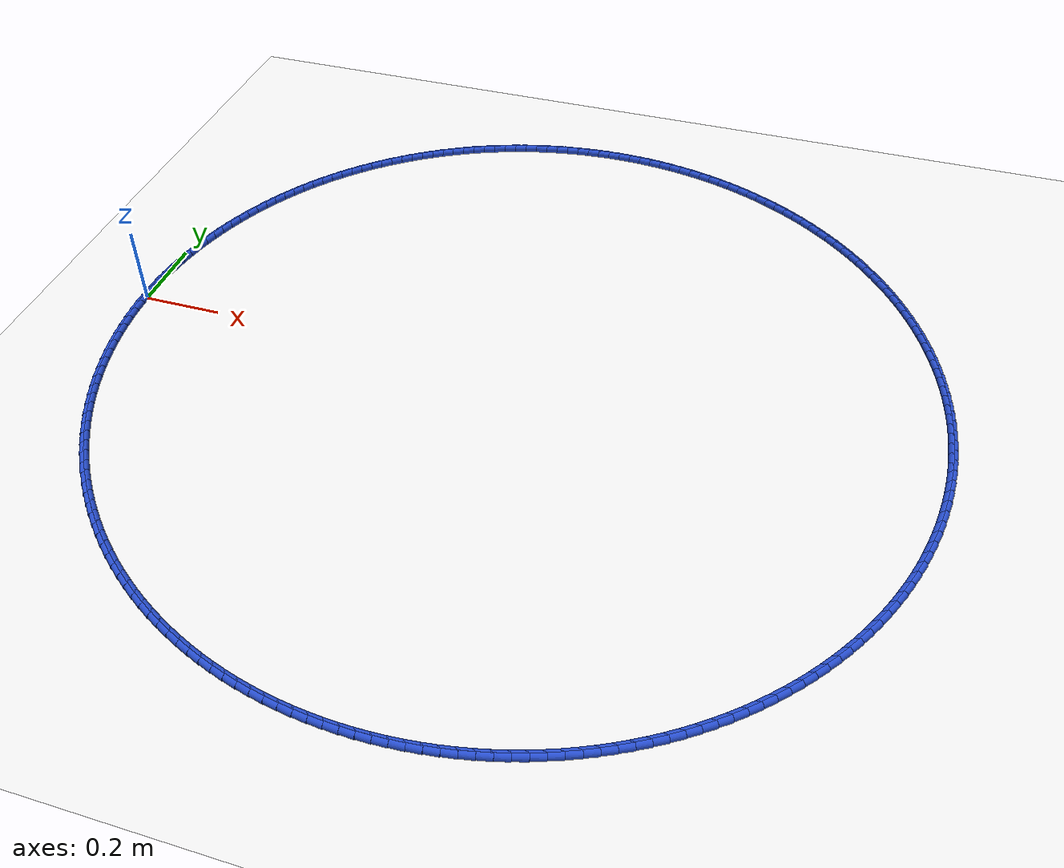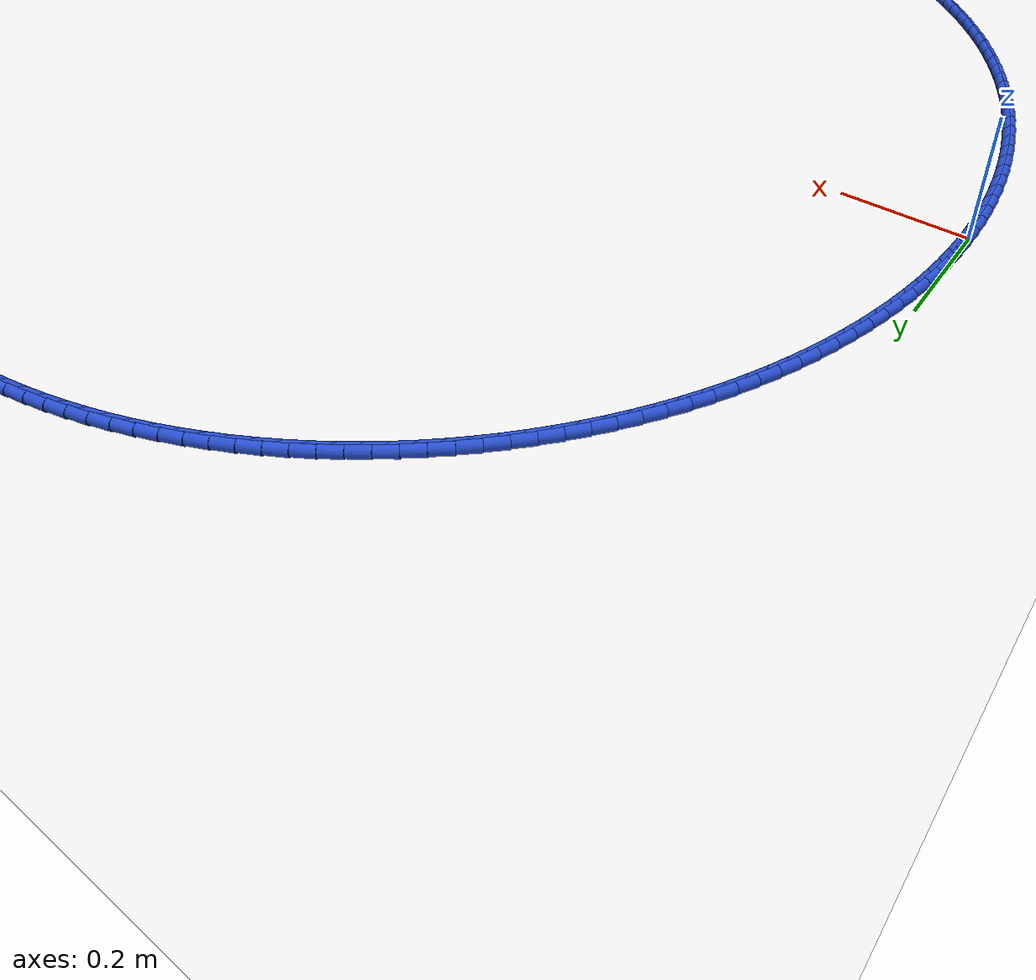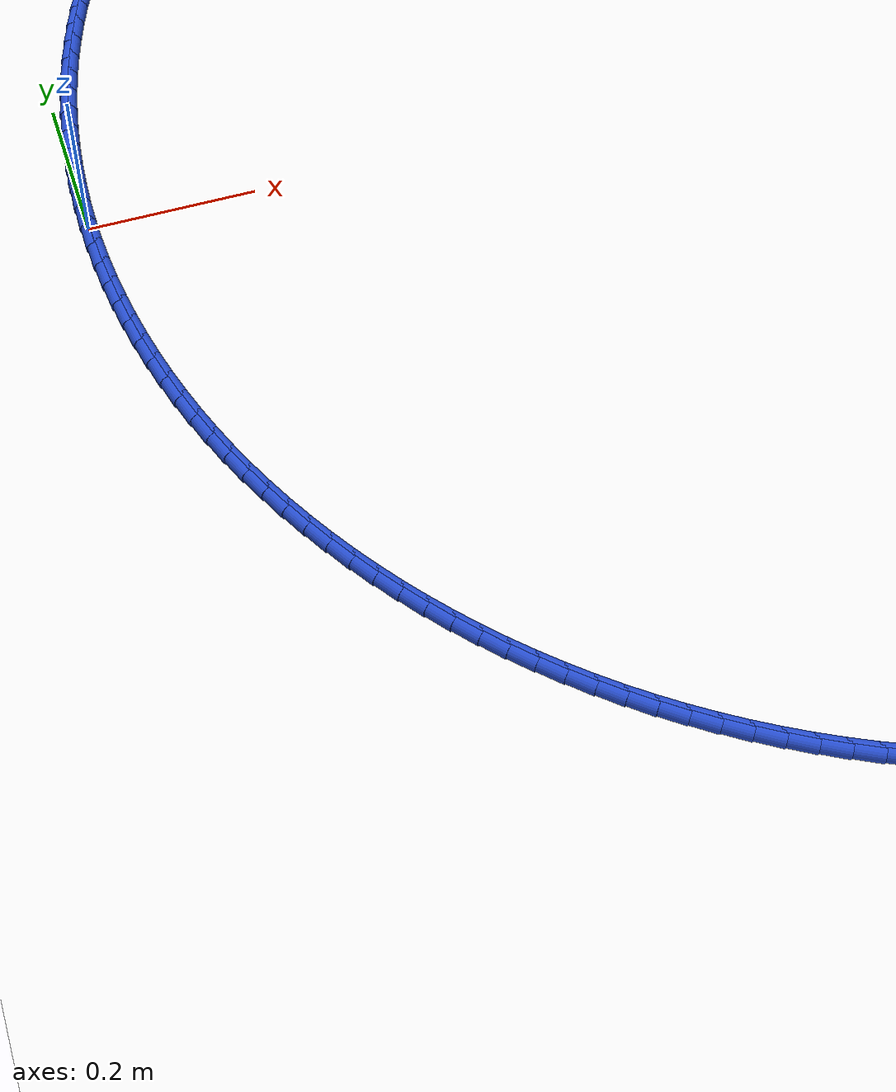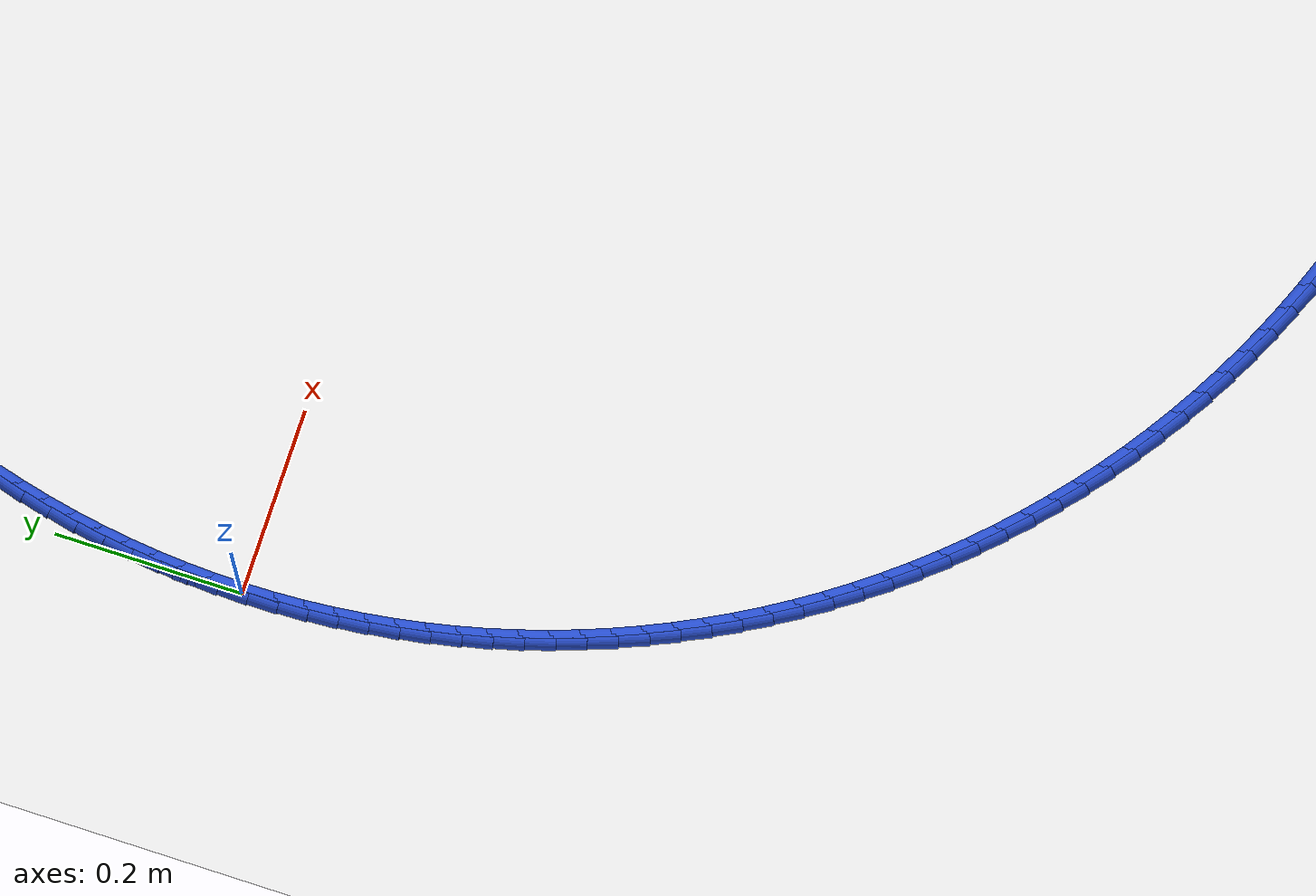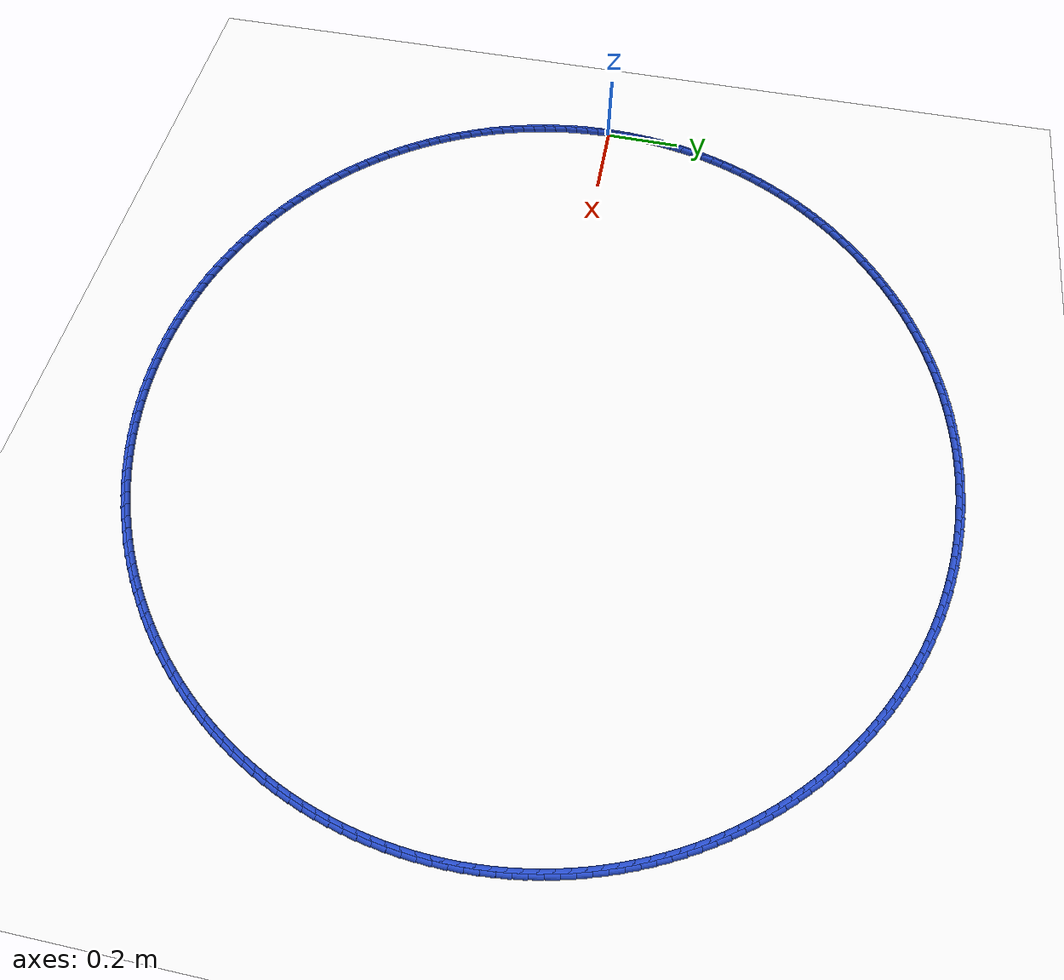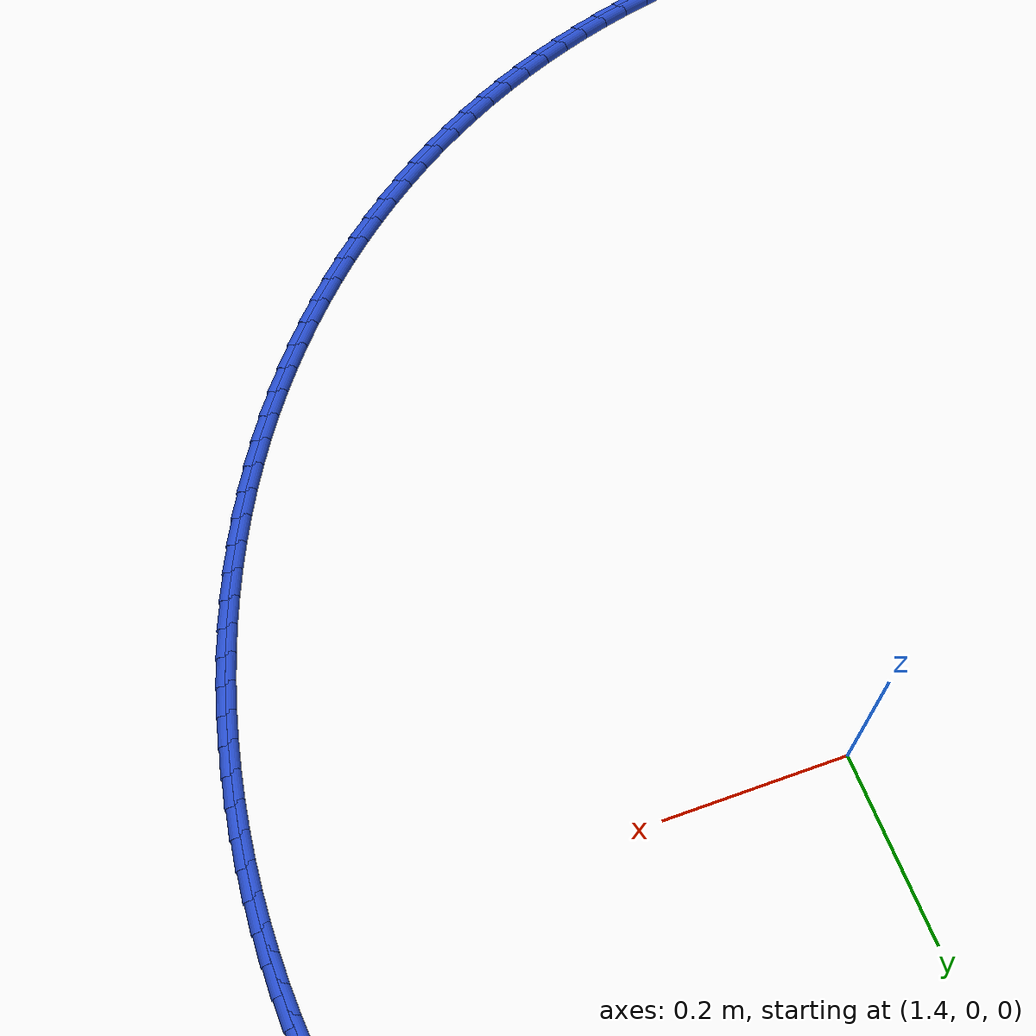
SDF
<sdf version="1.6">
 <world name="default">
  <light name="sun" type="directional">
   <pose>0 0 10 0 -0 0</pose>
   <diffuse>0.8 0.8 0.8 1</diffuse>
   <specular>0.2 0.2 0.2 1</specular>
   <attenuation>
    <range>1000</range>
    <constant>0.9</constant>
    <linear>0.01</linear>
    <quadratic>0.001</quadratic>
   </attenuation>
   <direction>-0.5 0.1 -0.9</direction>
  </light>
  <model name="ground_plane">
   <static>1</static>
   <link name="link">
    <collision name="collision">
     <geometry><plane><normal>0 0 1</normal><size>100 100</size></plane></geometry>
     <surface><friction><ode><mu>100</mu><mu2>50</mu2></ode></friction></surface>
    </collision>
    <visual name="visual">
     <cast_shadows>0</cast_shadows>
     <geometry><plane><normal>0 0 1</normal><size>100 100</size></plane></geometry>
     <material>
      <script><uri>file://media/materials/scripts/gazebo.material</uri><name>Gazebo/WhiteGlow</name></script>
     </material>
    </visual>
   </link>
  </model>
  <gravity>0 0 -9.8</gravity>
  <magnetic_field>6e-06 2.3e-05 -4.2e-05</magnetic_field>
  <atmosphere type="adiabatic"/>
  <physics name="default_physics" default="0" type="ode">
   <max_step_size>0.001</max_step_size>
   <real_time_factor>1</real_time_factor>
   <real_time_update_rate>1000</real_time_update_rate>
  </physics>
  <scene><ambient>0.4 0.4 0.4 1</ambient><background>0.7 0.7 0.7 1</background><shadows>1</shadows></scene>
  <spherical_coordinates>
   <surface_model>EARTH_WGS84</surface_model>
   <latitude_deg>0</latitude_deg>
   <longitude_deg>0</longitude_deg>
   <elevation>0</elevation>
   <heading_deg>0</heading_deg>
  </spherical_coordinates>
  <model name="line">
   <static>1</static>
   <link name="link_0">
    <pose>-1.734723475976807e-18 -4.163336342344337e-17 0.01 0 1.57 1.5549824605830722</pose>
    <collision name="collision">
     <geometry><cylinder><radius>0.01</radius><length>0.08</length></cylinder></geometry>
    </collision>
    <visual name="visual">
     <material>
      <script><name>Gazebo/Blue</name><uri>file://media/materials/scripts/gazebo.material</uri></script>
     </material>
     <geometry><cylinder><radius>0.01</radius><length>0.08</length></cylinder></geometry>
    </visual>
   </link>
   <static>1</static>
   <link name="link_1">
    <pose>0.0004967404176957579 0.03140908126714605 0.01 0 1.57 1.5234431790212397</pose>
    <collision name="collision">
     <geometry><cylinder><radius>0.01</radius><length>0.08</length></cylinder></geometry>
    </collision>
    <visual name="visual">
     <material>
      <script><name>Gazebo/Blue</name><uri>file://media/materials/scripts/gazebo.material</uri></script>
     </material>
     <geometry><cylinder><radius>0.01</radius><length>0.08</length></cylinder></geometry>
    </visual>
   </link>
   <static>1</static>
   <link name="link_2">
    <pose>0.001983714746050896 0.06278741212037388 0.01 0 1.57 1.492013745148784</pose>
    <collision name="collision">
     <geometry><cylinder><radius>0.01</radius><length>0.08</length></cylinder></geometry>
    </collision>
    <visual name="visual">
     <material>
      <script><name>Gazebo/Blue</name><uri>file://media/materials/scripts/gazebo.material</uri></script>
     </material>
     <geometry><cylinder><radius>0.01</radius><length>0.08</length></cylinder></geometry>
    </visual>
   </link>
   <static>1</static>
   <link name="link_3">
    <pose>0.004456052597967216 0.09410424214576518 0.01 0 1.57 1.460663230333921</pose>
    <collision name="collision">
     <geometry><cylinder><radius>0.01</radius><length>0.08</length></cylinder></geometry>
    </collision>
    <visual name="visual">
     <material>
      <script><name>Gazebo/Blue</name><uri>file://media/materials/scripts/gazebo.material</uri></script>
     </material>
     <geometry><cylinder><radius>0.01</radius><length>0.08</length></cylinder></geometry>
    </visual>
   </link>
   <static>1</static>
   <link name="link_4">
    <pose>0.007908883586346534 0.1253288209294017 0.01 0 1.57 1.4293602481064798</pose>
    <collision name="collision">
     <geometry><cylinder><radius>0.01</radius><length>0.08</length></cylinder></geometry>
    </collision>
    <visual name="visual">
     <material>
      <script><name>Gazebo/Blue</name><uri>file://media/materials/scripts/gazebo.material</uri></script>
     </material>
     <geometry><cylinder><radius>0.01</radius><length>0.08</length></cylinder></geometry>
    </visual>
   </link>
   <static>1</static>
   <link name="link_5">
    <pose>0.012337337324090649 0.15643039805736514 0.01 0 1.57 1.3980731401243338</pose>
    <collision name="collision">
     <geometry><cylinder><radius>0.01</radius><length>0.08</length></cylinder></geometry>
    </collision>
    <visual name="visual">
     <material>
      <script><name>Gazebo/Blue</name><uri>file://media/materials/scripts/gazebo.material</uri></script>
     </material>
     <geometry><cylinder><radius>0.01</radius><length>0.08</length></cylinder></geometry>
    </visual>
   </link>
   <static>1</static>
   <link name="link_6">
    <pose>0.017736543424101373 0.18737822311573732 0.01 0 1.57 1.3667701578968918</pose>
    <collision name="collision">
     <geometry><cylinder><radius>0.01</radius><length>0.08</length></cylinder></geometry>
    </collision>
    <visual name="visual">
     <material>
      <script><name>Gazebo/Blue</name><uri>file://media/materials/scripts/gazebo.material</uri></script>
     </material>
     <geometry><cylinder><radius>0.01</radius><length>0.08</length></cylinder></geometry>
    </visual>
   </link>
   <static>1</static>
   <link name="link_7">
    <pose>0.024101631499280515 0.21814154569059982 0.01 0 1.57 1.33541964308203</pose>
    <collision name="collision">
     <geometry><cylinder><radius>0.01</radius><length>0.08</length></cylinder></geometry>
    </collision>
    <visual name="visual">
     <material>
      <script><name>Gazebo/Blue</name><uri>file://media/materials/scripts/gazebo.material</uri></script>
     </material>
     <geometry><cylinder><radius>0.01</radius><length>0.08</length></cylinder></geometry>
    </visual>
   </link>
   <static>1</static>
   <link name="link_8">
    <pose>0.03142773116252987 0.24868961536803458 0.01 0 1.57 1.3039902092095739</pose>
    <collision name="collision">
     <geometry><cylinder><radius>0.01</radius><length>0.08</length></cylinder></geometry>
    </collision>
    <visual name="visual">
     <material>
      <script><name>Gazebo/Blue</name><uri>file://media/materials/scripts/gazebo.material</uri></script>
     </material>
     <geometry><cylinder><radius>0.01</radius><length>0.08</length></cylinder></geometry>
    </visual>
   </link>
   <static>1</static>
   <link name="link_9">
    <pose>0.03970997202675125 0.27899168173412314 0.01 0 1.57 1.2724509276477411</pose>
    <collision name="collision">
     <geometry><cylinder><radius>0.01</radius><length>0.08</length></cylinder></geometry>
    </collision>
    <visual name="visual">
     <material>
      <script><name>Gazebo/Blue</name><uri>file://media/materials/scripts/gazebo.material</uri></script>
     </material>
     <geometry><cylinder><radius>0.01</radius><length>0.08</length></cylinder></geometry>
    </visual>
   </link>
   <static>1</static>
   <link name="link_10">
    <pose>0.0489434837048465 0.3090169943749474 0.01 0 1.57 1.240823195224093</pose>
    <collision name="collision">
     <geometry><cylinder><radius>0.01</radius><length>0.08</length></cylinder></geometry>
    </collision>
    <visual name="visual">
     <material>
      <script><name>Gazebo/Blue</name><uri>file://media/materials/scripts/gazebo.material</uri></script>
     </material>
     <geometry><cylinder><radius>0.01</radius><length>0.08</length></cylinder></geometry>
    </visual>
   </link>
   <static>1</static>
   <link name="link_11">
    <pose>0.05912185180525515 0.33873530455404977 0.01 0 1.57 1.2092839136622617</pose>
    <collision name="collision">
     <geometry><cylinder><radius>0.01</radius><length>0.08</length></cylinder></geometry>
    </collision>
    <visual name="visual">
     <material>
      <script><name>Gazebo/Blue</name><uri>file://media/materials/scripts/gazebo.material</uri></script>
     </material>
     <geometry><cylinder><radius>0.01</radius><length>0.08</length></cylinder></geometry>
    </visual>
   </link>
   <static>1</static>
   <link name="link_12">
    <pose>0.07023248591856804 0.3681183702448164 0.01 0 1.57 1.1778544797898043</pose>
    <collision name="collision">
     <geometry><cylinder><radius>0.01</radius><length>0.08</length></cylinder></geometry>
    </collision>
    <visual name="visual">
     <material>
      <script><name>Gazebo/Blue</name><uri>file://media/materials/scripts/gazebo.material</uri></script>
     </material>
     <geometry><cylinder><radius>0.01</radius><length>0.08</length></cylinder></geometry>
    </visual>
   </link>
   <static>1</static>
   <link name="link_13">
    <pose>0.08226125163091373 0.39713845109809387 0.01 0 1.57 1.1465039649749418</pose>
    <collision name="collision">
     <geometry><cylinder><radius>0.01</radius><length>0.08</length></cylinder></geometry>
    </collision>
    <visual name="visual">
     <material>
      <script><name>Gazebo/Blue</name><uri>file://media/materials/scripts/gazebo.material</uri></script>
     </material>
     <geometry><cylinder><radius>0.01</radius><length>0.08</length></cylinder></geometry>
    </visual>
   </link>
   <static>1</static>
   <link name="link_14">
    <pose>0.0951940145284208 0.4257678067647291 0.01 0 1.57 1.1152009827475025</pose>
    <collision name="collision">
     <geometry><cylinder><radius>0.01</radius><length>0.08</length></cylinder></geometry>
    </collision>
    <visual name="visual">
     <material>
      <script><name>Gazebo/Blue</name><uri>file://media/materials/scripts/gazebo.material</uri></script>
     </material>
     <geometry><cylinder><radius>0.01</radius><length>0.08</length></cylinder></geometry>
    </visual>
   </link>
   <static>1</static>
   <link name="link_15">
    <pose>0.10901664019721781 0.4539786968955689 0.01 0 1.57 1.0839138747653538</pose>
    <collision name="collision">
     <geometry><cylinder><radius>0.01</radius><length>0.08</length></cylinder></geometry>
    </collision>
    <visual name="visual">
     <material>
      <script><name>Gazebo/Blue</name><uri>file://media/materials/scripts/gazebo.material</uri></script>
     </material>
     <geometry><cylinder><radius>0.01</radius><length>0.08</length></cylinder></geometry>
    </visual>
   </link>
   <static>1</static>
   <link name="link_16">
    <pose>0.12371499422343338 0.4817433811414599 0.01 0 1.57 1.0526108925379154</pose>
    <collision name="collision">
     <geometry><cylinder><radius>0.01</radius><length>0.08</length></cylinder></geometry>
    </collision>
    <visual name="visual">
     <material>
      <script><name>Gazebo/Blue</name><uri>file://media/materials/scripts/gazebo.material</uri></script>
     </material>
     <geometry><cylinder><radius>0.01</radius><length>0.08</length></cylinder></geometry>
    </visual>
   </link>
   <static>1</static>
   <link name="link_17">
    <pose>0.13927494219319608 0.5090341191532493 0.01 0 1.57 1.0212603777230493</pose>
    <collision name="collision">
     <geometry><cylinder><radius>0.01</radius><length>0.08</length></cylinder></geometry>
    </collision>
    <visual name="visual">
     <material>
      <script><name>Gazebo/Blue</name><uri>file://media/materials/scripts/gazebo.material</uri></script>
     </material>
     <geometry><cylinder><radius>0.01</radius><length>0.08</length></cylinder></geometry>
    </visual>
   </link>
   <static>1</static>
   <link name="link_18">
    <pose>0.15568234969263436 0.5358231705817831 0.01 0 1.57 0.9898309438505934</pose>
    <collision name="collision">
     <geometry><cylinder><radius>0.01</radius><length>0.08</length></cylinder></geometry>
    </collision>
    <visual name="visual">
     <material>
      <script><name>Gazebo/Blue</name><uri>file://media/materials/scripts/gazebo.material</uri></script>
     </material>
     <geometry><cylinder><radius>0.01</radius><length>0.08</length></cylinder></geometry>
    </visual>
   </link>
   <static>1</static>
   <link name="link_19">
    <pose>0.17292308230787706 0.5620827950779088 0.01 0 1.57 0.9582916622887631</pose>
    <collision name="collision">
     <geometry><cylinder><radius>0.01</radius><length>0.08</length></cylinder></geometry>
    </collision>
    <visual name="visual">
     <material>
      <script><name>Gazebo/Blue</name><uri>file://media/materials/scripts/gazebo.material</uri></script>
     </material>
     <geometry><cylinder><radius>0.01</radius><length>0.08</length></cylinder></geometry>
    </visual>
   </link>
   <static>1</static>
   <link name="link_20">
    <pose>0.19098300562505255 0.587785252292473 0.01 0 1.57 0.9266639298651125</pose>
    <collision name="collision">
     <geometry><cylinder><radius>0.01</radius><length>0.08</length></cylinder></geometry>
    </collision>
    <visual name="visual">
     <material>
      <script><name>Gazebo/Blue</name><uri>file://media/materials/scripts/gazebo.material</uri></script>
     </material>
     <geometry><cylinder><radius>0.01</radius><length>0.08</length></cylinder></geometry>
    </visual>
   </link>
   <static>1</static>
   <link name="link_21">
    <pose>0.20984667182164554 0.6129037561235587 0.01 0 1.57 0.8951246483032806</pose>
    <collision name="collision">
     <geometry><cylinder><radius>0.01</radius><length>0.08</length></cylinder></geometry>
    </collision>
    <visual name="visual">
     <material>
      <script><name>Gazebo/Blue</name><uri>file://media/materials/scripts/gazebo.material</uri></script>
     </material>
     <geometry><cylinder><radius>0.01</radius><length>0.08</length></cylinder></geometry>
    </visual>
   </link>
   <static>1</static>
   <link name="link_22">
    <pose>0.22949337944056533 0.6374153374581951 0.01 0 1.57 0.8636952144308283</pose>
    <collision name="collision">
     <geometry><cylinder><radius>0.01</radius><length>0.08</length></cylinder></geometry>
    </collision>
    <visual name="visual">
     <material>
      <script><name>Gazebo/Blue</name><uri>file://media/materials/scripts/gazebo.material</uri></script>
     </material>
     <geometry><cylinder><radius>0.01</radius><length>0.08</length></cylinder></geometry>
    </visual>
   </link>
   <static>1</static>
   <link name="link_23">
    <pose>0.2499011136160772 0.6612979814306476 0.01 0 1.57 0.8323446996159628</pose>
    <collision name="collision">
     <geometry><cylinder><radius>0.01</radius><length>0.08</length></cylinder></geometry>
    </collision>
    <visual name="visual">
     <material>
      <script><name>Gazebo/Blue</name><uri>file://media/materials/scripts/gazebo.material</uri></script>
     </material>
     <geometry><cylinder><radius>0.01</radius><length>0.08</length></cylinder></geometry>
    </visual>
   </link>
   <static>1</static>
   <link name="link_24">
    <pose>0.2710478594824465 0.6845296731751811 0.01 0 1.57 0.801041717388523</pose>
    <collision name="collision">
     <geometry><cylinder><radius>0.01</radius><length>0.08</length></cylinder></geometry>
    </collision>
    <visual name="visual">
     <material>
      <script><name>Gazebo/Blue</name><uri>file://media/materials/scripts/gazebo.material</uri></script>
     </material>
     <geometry><cylinder><radius>0.01</radius><length>0.08</length></cylinder></geometry>
    </visual>
   </link>
   <static>1</static>
   <link name="link_25">
    <pose>0.2929116021739386 0.7070883978260614 0.01 0 1.57 0.7697546094063747</pose>
    <collision name="collision">
     <geometry><cylinder><radius>0.01</radius><length>0.08</length></cylinder></geometry>
    </collision>
    <visual name="visual">
     <material>
      <script><name>Gazebo/Blue</name><uri>file://media/materials/scripts/gazebo.material</uri></script>
     </material>
     <geometry><cylinder><radius>0.01</radius><length>0.08</length></cylinder></geometry>
    </visual>
   </link>
   <static>1</static>
   <link name="link_26">
    <pose>0.31547032682481874 0.7289521405175534 0.01 0 1.57 0.738451627178934</pose>
    <collision name="collision">
     <geometry><cylinder><radius>0.01</radius><length>0.08</length></cylinder></geometry>
    </collision>
    <visual name="visual">
     <material>
      <script><name>Gazebo/Blue</name><uri>file://media/materials/scripts/gazebo.material</uri></script>
     </material>
     <geometry><cylinder><radius>0.01</radius><length>0.08</length></cylinder></geometry>
    </visual>
   </link>
   <static>1</static>
   <link name="link_27">
    <pose>0.33870201856935234 0.7500988863839227 0.01 0 1.57 0.7071011123640703</pose>
    <collision name="collision">
     <geometry><cylinder><radius>0.01</radius><length>0.08</length></cylinder></geometry>
    </collision>
    <visual name="visual">
     <material>
      <script><name>Gazebo/Blue</name><uri>file://media/materials/scripts/gazebo.material</uri></script>
     </material>
     <geometry><cylinder><radius>0.01</radius><length>0.08</length></cylinder></geometry>
    </visual>
   </link>
   <static>1</static>
   <link name="link_28">
    <pose>0.3625846625418047 0.7705066205594346 0.01 0 1.57 0.675671678491614</pose>
    <collision name="collision">
     <geometry><cylinder><radius>0.01</radius><length>0.08</length></cylinder></geometry>
    </collision>
    <visual name="visual">
     <material>
      <script><name>Gazebo/Blue</name><uri>file://media/materials/scripts/gazebo.material</uri></script>
     </material>
     <geometry><cylinder><radius>0.01</radius><length>0.08</length></cylinder></geometry>
    </visual>
   </link>
   <static>1</static>
   <link name="link_29">
    <pose>0.387096243876441 0.7901533281783543 0.01 0 1.57 0.6441323969297859</pose>
    <collision name="collision">
     <geometry><cylinder><radius>0.01</radius><length>0.08</length></cylinder></geometry>
    </collision>
    <visual name="visual">
     <material>
      <script><name>Gazebo/Blue</name><uri>file://media/materials/scripts/gazebo.material</uri></script>
     </material>
     <geometry><cylinder><radius>0.01</radius><length>0.08</length></cylinder></geometry>
    </visual>
   </link>
   <static>1</static>
   <link name="link_30">
    <pose>0.41221474770752686 0.8090169943749475 0.01 0 1.57 0.6125046645061313</pose>
    <collision name="collision">
     <geometry><cylinder><radius>0.01</radius><length>0.08</length></cylinder></geometry>
    </collision>
    <visual name="visual">
     <material>
      <script><name>Gazebo/Blue</name><uri>file://media/materials/scripts/gazebo.material</uri></script>
     </material>
     <geometry><cylinder><radius>0.01</radius><length>0.08</length></cylinder></geometry>
    </visual>
   </link>
   <static>1</static>
   <link name="link_31">
    <pose>0.43791720492209096 0.8270769176921228 0.01 0 1.57 0.5809653829443019</pose>
    <collision name="collision">
     <geometry><cylinder><radius>0.01</radius><length>0.08</length></cylinder></geometry>
    </collision>
    <visual name="visual">
     <material>
      <script><name>Gazebo/Blue</name><uri>file://media/materials/scripts/gazebo.material</uri></script>
     </material>
     <geometry><cylinder><radius>0.01</radius><length>0.08</length></cylinder></geometry>
    </visual>
   </link>
   <static>1</static>
   <link name="link_32">
    <pose>0.4641768294182168 0.8443176503073655 0.01 0 1.57 0.5495359490718427</pose>
    <collision name="collision">
     <geometry><cylinder><radius>0.01</radius><length>0.08</length></cylinder></geometry>
    </collision>
    <visual name="visual">
     <material>
      <script><name>Gazebo/Blue</name><uri>file://media/materials/scripts/gazebo.material</uri></script>
     </material>
     <geometry><cylinder><radius>0.01</radius><length>0.08</length></cylinder></geometry>
    </visual>
   </link>
   <static>1</static>
   <link name="link_33">
    <pose>0.4909658808467507 0.8607250578068036 0.01 0 1.57 0.5181854342569836</pose>
    <collision name="collision">
     <geometry><cylinder><radius>0.01</radius><length>0.08</length></cylinder></geometry>
    </collision>
    <visual name="visual">
     <material>
      <script><name>Gazebo/Blue</name><uri>file://media/materials/scripts/gazebo.material</uri></script>
     </material>
     <geometry><cylinder><radius>0.01</radius><length>0.08</length></cylinder></geometry>
    </visual>
   </link>
   <static>1</static>
   <link name="link_34">
    <pose>0.51825661885854 0.8762850057765664 0.01 0 1.57 0.4868824520295401</pose>
    <collision name="collision">
     <geometry><cylinder><radius>0.01</radius><length>0.08</length></cylinder></geometry>
    </collision>
    <visual name="visual">
     <material>
      <script><name>Gazebo/Blue</name><uri>file://media/materials/scripts/gazebo.material</uri></script>
     </material>
     <geometry><cylinder><radius>0.01</radius><length>0.08</length></cylinder></geometry>
    </visual>
   </link>
   <static>1</static>
   <link name="link_35">
    <pose>0.546021303104431 0.8909833598027819 0.01 0 1.57 0.4555953440474025</pose>
    <collision name="collision">
     <geometry><cylinder><radius>0.01</radius><length>0.08</length></cylinder></geometry>
    </collision>
    <visual name="visual">
     <material>
      <script><name>Gazebo/Blue</name><uri>file://media/materials/scripts/gazebo.material</uri></script>
     </material>
     <geometry><cylinder><radius>0.01</radius><length>0.08</length></cylinder></geometry>
    </visual>
   </link>
   <static>1</static>
   <link name="link_36">
    <pose>0.5742321932352706 0.9048059854715791 0.01 0 1.57 0.424292361819947</pose>
    <collision name="collision">
     <geometry><cylinder><radius>0.01</radius><length>0.08</length></cylinder></geometry>
    </collision>
    <visual name="visual">
     <material>
      <script><name>Gazebo/Blue</name><uri>file://media/materials/scripts/gazebo.material</uri></script>
     </material>
     <geometry><cylinder><radius>0.01</radius><length>0.08</length></cylinder></geometry>
    </visual>
   </link>
   <static>1</static>
   <link name="link_37">
    <pose>0.6028615489019058 0.9177387483690859 0.01 0 1.57 0.3929418470050872</pose>
    <collision name="collision">
     <geometry><cylinder><radius>0.01</radius><length>0.08</length></cylinder></geometry>
    </collision>
    <visual name="visual">
     <material>
      <script><name>Gazebo/Blue</name><uri>file://media/materials/scripts/gazebo.material</uri></script>
     </material>
     <geometry><cylinder><radius>0.01</radius><length>0.08</length></cylinder></geometry>
    </visual>
   </link>
   <static>1</static>
   <link name="link_38">
    <pose>0.6318816297551834 0.9297675140814314 0.01 0 1.57 0.3615124131326446</pose>
    <collision name="collision">
     <geometry><cylinder><radius>0.01</radius><length>0.08</length></cylinder></geometry>
    </collision>
    <visual name="visual">
     <material>
      <script><name>Gazebo/Blue</name><uri>file://media/materials/scripts/gazebo.material</uri></script>
     </material>
     <geometry><cylinder><radius>0.01</radius><length>0.08</length></cylinder></geometry>
    </visual>
   </link>
   <static>1</static>
   <link name="link_39">
    <pose>0.6612646954459501 0.9408781481947447 0.01 0 1.57 0.32997313157079977</pose>
    <collision name="collision">
     <geometry><cylinder><radius>0.01</radius><length>0.08</length></cylinder></geometry>
    </collision>
    <visual name="visual">
     <material>
      <script><name>Gazebo/Blue</name><uri>file://media/materials/scripts/gazebo.material</uri></script>
     </material>
     <geometry><cylinder><radius>0.01</radius><length>0.08</length></cylinder></geometry>
    </visual>
   </link>
   <static>1</static>
   <link name="link_40">
    <pose>0.6909830056250524 0.9510565162951532 0.01 0 1.57 0.2983453991471443</pose>
    <collision name="collision">
     <geometry><cylinder><radius>0.01</radius><length>0.08</length></cylinder></geometry>
    </collision>
    <visual name="visual">
     <material>
      <script><name>Gazebo/Blue</name><uri>file://media/materials/scripts/gazebo.material</uri></script>
     </material>
     <geometry><cylinder><radius>0.01</radius><length>0.08</length></cylinder></geometry>
    </visual>
   </link>
   <static>1</static>
   <link name="link_41">
    <pose>0.7210083182658765 0.960290027973248 0.01 0 1.57 0.2668061175853348</pose>
    <collision name="collision">
     <geometry><cylinder><radius>0.01</radius><length>0.08</length></cylinder></geometry>
    </collision>
    <visual name="visual">
     <material>
      <script><name>Gazebo/Blue</name><uri>file://media/materials/scripts/gazebo.material</uri></script>
     </material>
     <geometry><cylinder><radius>0.01</radius><length>0.08</length></cylinder></geometry>
    </visual>
   </link>
   <static>1</static>
   <link name="link_42">
    <pose>0.7513103846319652 0.9685722688374698 0.01 0 1.57 0.23537668371286743</pose>
    <collision name="collision">
     <geometry><cylinder><radius>0.01</radius><length>0.08</length></cylinder></geometry>
    </collision>
    <visual name="visual">
     <material>
      <script><name>Gazebo/Blue</name><uri>file://media/materials/scripts/gazebo.material</uri></script>
     </material>
     <geometry><cylinder><radius>0.01</radius><length>0.08</length></cylinder></geometry>
    </visual>
   </link>
   <static>1</static>
   <link name="link_43">
    <pose>0.7818584543093999 0.9758983685007192 0.01 0 1.57 0.204026168898003</pose>
    <collision name="collision">
     <geometry><cylinder><radius>0.01</radius><length>0.08</length></cylinder></geometry>
    </collision>
    <visual name="visual">
     <material>
      <script><name>Gazebo/Blue</name><uri>file://media/materials/scripts/gazebo.material</uri></script>
     </material>
     <geometry><cylinder><radius>0.01</radius><length>0.08</length></cylinder></geometry>
    </visual>
   </link>
   <static>1</static>
   <link name="link_44">
    <pose>0.8126217768842625 0.9822634565758983 0.01 0 1.57 0.17272318667056447</pose>
    <collision name="collision">
     <geometry><cylinder><radius>0.01</radius><length>0.08</length></cylinder></geometry>
    </collision>
    <visual name="visual">
     <material>
      <script><name>Gazebo/Blue</name><uri>file://media/materials/scripts/gazebo.material</uri></script>
     </material>
     <geometry><cylinder><radius>0.01</radius><length>0.08</length></cylinder></geometry>
    </visual>
   </link>
   <static>1</static>
   <link name="link_45">
    <pose>0.8435696019426346 0.9876626626759091 0.01 0 1.57 0.14143607868841418</pose>
    <collision name="collision">
     <geometry><cylinder><radius>0.01</radius><length>0.08</length></cylinder></geometry>
    </collision>
    <visual name="visual">
     <material>
      <script><name>Gazebo/Blue</name><uri>file://media/materials/scripts/gazebo.material</uri></script>
     </material>
     <geometry><cylinder><radius>0.01</radius><length>0.08</length></cylinder></geometry>
    </visual>
   </link>
   <static>1</static>
   <link name="link_46">
    <pose>0.8746711790705981 0.9920911164136531 0.01 0 1.57 0.11013309646097294</pose>
    <collision name="collision">
     <geometry><cylinder><radius>0.01</radius><length>0.08</length></cylinder></geometry>
    </collision>
    <visual name="visual">
     <material>
      <script><name>Gazebo/Blue</name><uri>file://media/materials/scripts/gazebo.material</uri></script>
     </material>
     <geometry><cylinder><radius>0.01</radius><length>0.08</length></cylinder></geometry>
    </visual>
   </link>
   <static>1</static>
   <link name="link_47">
    <pose>0.9058957578542346 0.9955439474020323 0.01 0 1.57 0.07878258164611084</pose>
    <collision name="collision">
     <geometry><cylinder><radius>0.01</radius><length>0.08</length></cylinder></geometry>
    </collision>
    <visual name="visual">
     <material>
      <script><name>Gazebo/Blue</name><uri>file://media/materials/scripts/gazebo.material</uri></script>
     </material>
     <geometry><cylinder><radius>0.01</radius><length>0.08</length></cylinder></geometry>
    </visual>
   </link>
   <static>1</static>
   <link name="link_48">
    <pose>0.9372125878796257 0.9980162852539486 0.01 0 1.57 0.047353147773665796</pose>
    <collision name="collision">
     <geometry><cylinder><radius>0.01</radius><length>0.08</length></cylinder></geometry>
    </collision>
    <visual name="visual">
     <material>
      <script><name>Gazebo/Blue</name><uri>file://media/materials/scripts/gazebo.material</uri></script>
     </material>
     <geometry><cylinder><radius>0.01</radius><length>0.08</length></cylinder></geometry>
    </visual>
   </link>
   <static>1</static>
   <link name="link_49">
    <pose>0.9685909187328537 0.999503259582304 0.01 0 1.57 0.01581386621182451</pose>
    <collision name="collision">
     <geometry><cylinder><radius>0.01</radius><length>0.08</length></cylinder></geometry>
    </collision>
    <visual name="visual">
     <material>
      <script><name>Gazebo/Blue</name><uri>file://media/materials/scripts/gazebo.material</uri></script>
     </material>
     <geometry><cylinder><radius>0.01</radius><length>0.08</length></cylinder></geometry>
    </visual>
   </link>
   <static>1</static>
   <link name="link_50">
    <pose>0.9999999999999999 0.9999999999999998 0.01 0 1.57 -0.015813866211828096</pose>
    <collision name="collision">
     <geometry><cylinder><radius>0.01</radius><length>0.08</length></cylinder></geometry>
    </collision>
    <visual name="visual">
     <material>
      <script><name>Gazebo/Blue</name><uri>file://media/materials/scripts/gazebo.material</uri></script>
     </material>
     <geometry><cylinder><radius>0.01</radius><length>0.08</length></cylinder></geometry>
    </visual>
   </link>
   <static>1</static>
   <link name="link_51">
    <pose>1.031409081267146 0.9995032595823039 0.01 0 1.57 -0.04735314777366294</pose>
    <collision name="collision">
     <geometry><cylinder><radius>0.01</radius><length>0.08</length></cylinder></geometry>
    </collision>
    <visual name="visual">
     <material>
      <script><name>Gazebo/Blue</name><uri>file://media/materials/scripts/gazebo.material</uri></script>
     </material>
     <geometry><cylinder><radius>0.01</radius><length>0.08</length></cylinder></geometry>
    </visual>
   </link>
   <static>1</static>
   <link name="link_52">
    <pose>1.0627874121203735 0.9980162852539486 0.01 0 1.57 -0.07878258164609832</pose>
    <collision name="collision">
     <geometry><cylinder><radius>0.01</radius><length>0.08</length></cylinder></geometry>
    </collision>
    <visual name="visual">
     <material>
      <script><name>Gazebo/Blue</name><uri>file://media/materials/scripts/gazebo.material</uri></script>
     </material>
     <geometry><cylinder><radius>0.01</radius><length>0.08</length></cylinder></geometry>
    </visual>
   </link>
   <static>1</static>
   <link name="link_53">
    <pose>1.0941042421457654 0.9955439474020327 0.01 0 1.57 -0.11013309646098346</pose>
    <collision name="collision">
     <geometry><cylinder><radius>0.01</radius><length>0.08</length></cylinder></geometry>
    </collision>
    <visual name="visual">
     <material>
      <script><name>Gazebo/Blue</name><uri>file://media/materials/scripts/gazebo.material</uri></script>
     </material>
     <geometry><cylinder><radius>0.01</radius><length>0.08</length></cylinder></geometry>
    </visual>
   </link>
   <static>1</static>
   <link name="link_54">
    <pose>1.125328820929402 0.9920911164136531 0.01 0 1.57 -0.14143607868842215</pose>
    <collision name="collision">
     <geometry><cylinder><radius>0.01</radius><length>0.08</length></cylinder></geometry>
    </collision>
    <visual name="visual">
     <material>
      <script><name>Gazebo/Blue</name><uri>file://media/materials/scripts/gazebo.material</uri></script>
     </material>
     <geometry><cylinder><radius>0.01</radius><length>0.08</length></cylinder></geometry>
    </visual>
   </link>
   <static>1</static>
   <link name="link_55">
    <pose>1.1564303980573651 0.9876626626759089 0.01 0 1.57 -0.1727231866705516</pose>
    <collision name="collision">
     <geometry><cylinder><radius>0.01</radius><length>0.08</length></cylinder></geometry>
    </collision>
    <visual name="visual">
     <material>
      <script><name>Gazebo/Blue</name><uri>file://media/materials/scripts/gazebo.material</uri></script>
     </material>
     <geometry><cylinder><radius>0.01</radius><length>0.08</length></cylinder></geometry>
    </visual>
   </link>
   <static>1</static>
   <link name="link_56">
    <pose>1.1873782231157377 0.9822634565758984 0.01 0 1.57 -0.2040261688980037</pose>
    <collision name="collision">
     <geometry><cylinder><radius>0.01</radius><length>0.08</length></cylinder></geometry>
    </collision>
    <visual name="visual">
     <material>
      <script><name>Gazebo/Blue</name><uri>file://media/materials/scripts/gazebo.material</uri></script>
     </material>
     <geometry><cylinder><radius>0.01</radius><length>0.08</length></cylinder></geometry>
    </visual>
   </link>
   <static>1</static>
   <link name="link_57">
    <pose>1.2181415456906002 0.9758983685007193 0.01 0 1.57 -0.23537668371287074</pose>
    <collision name="collision">
     <geometry><cylinder><radius>0.01</radius><length>0.08</length></cylinder></geometry>
    </collision>
    <visual name="visual">
     <material>
      <script><name>Gazebo/Blue</name><uri>file://media/materials/scripts/gazebo.material</uri></script>
     </material>
     <geometry><cylinder><radius>0.01</radius><length>0.08</length></cylinder></geometry>
    </visual>
   </link>
   <static>1</static>
   <link name="link_58">
    <pose>1.2486896153680345 0.9685722688374699 0.01 0 1.57 -0.2668061175853245</pose>
    <collision name="collision">
     <geometry><cylinder><radius>0.01</radius><length>0.08</length></cylinder></geometry>
    </collision>
    <visual name="visual">
     <material>
      <script><name>Gazebo/Blue</name><uri>file://media/materials/scripts/gazebo.material</uri></script>
     </material>
     <geometry><cylinder><radius>0.01</radius><length>0.08</length></cylinder></geometry>
    </visual>
   </link>
   <static>1</static>
   <link name="link_59">
    <pose>1.2789916817341231 0.9602900279732485 0.01 0 1.57 -0.29834539914715236</pose>
    <collision name="collision">
     <geometry><cylinder><radius>0.01</radius><length>0.08</length></cylinder></geometry>
    </collision>
    <visual name="visual">
     <material>
      <script><name>Gazebo/Blue</name><uri>file://media/materials/scripts/gazebo.material</uri></script>
     </material>
     <geometry><cylinder><radius>0.01</radius><length>0.08</length></cylinder></geometry>
    </visual>
   </link>
   <static>1</static>
   <link name="link_60">
    <pose>1.3090169943749475 0.9510565162951533 0.01 0 1.57 -0.3299731315708098</pose>
    <collision name="collision">
     <geometry><cylinder><radius>0.01</radius><length>0.08</length></cylinder></geometry>
    </collision>
    <visual name="visual">
     <material>
      <script><name>Gazebo/Blue</name><uri>file://media/materials/scripts/gazebo.material</uri></script>
     </material>
     <geometry><cylinder><radius>0.01</radius><length>0.08</length></cylinder></geometry>
    </visual>
   </link>
   <static>1</static>
   <link name="link_61">
    <pose>1.3387353045540498 0.9408781481947445 0.01 0 1.57 -0.3615124131326438</pose>
    <collision name="collision">
     <geometry><cylinder><radius>0.01</radius><length>0.08</length></cylinder></geometry>
    </collision>
    <visual name="visual">
     <material>
      <script><name>Gazebo/Blue</name><uri>file://media/materials/scripts/gazebo.material</uri></script>
     </material>
     <geometry><cylinder><radius>0.01</radius><length>0.08</length></cylinder></geometry>
    </visual>
   </link>
   <static>1</static>
   <link name="link_62">
    <pose>1.3681183702448163 0.9297675140814313 0.01 0 1.57 -0.3929418470050913</pose>
    <collision name="collision">
     <geometry><cylinder><radius>0.01</radius><length>0.08</length></cylinder></geometry>
    </collision>
    <visual name="visual">
     <material>
      <script><name>Gazebo/Blue</name><uri>file://media/materials/scripts/gazebo.material</uri></script>
     </material>
     <geometry><cylinder><radius>0.01</radius><length>0.08</length></cylinder></geometry>
    </visual>
   </link>
   <static>1</static>
   <link name="link_63">
    <pose>1.3971384510980935 0.9177387483690858 0.01 0 1.57 -0.4242923618199552</pose>
    <collision name="collision">
     <geometry><cylinder><radius>0.01</radius><length>0.08</length></cylinder></geometry>
    </collision>
    <visual name="visual">
     <material>
      <script><name>Gazebo/Blue</name><uri>file://media/materials/scripts/gazebo.material</uri></script>
     </material>
     <geometry><cylinder><radius>0.01</radius><length>0.08</length></cylinder></geometry>
    </visual>
   </link>
   <static>1</static>
   <link name="link_64">
    <pose>1.4257678067647288 0.9048059854715786 0.01 0 1.57 -0.4555953440473946</pose>
    <collision name="collision">
     <geometry><cylinder><radius>0.01</radius><length>0.08</length></cylinder></geometry>
    </collision>
    <visual name="visual">
     <material>
      <script><name>Gazebo/Blue</name><uri>file://media/materials/scripts/gazebo.material</uri></script>
     </material>
     <geometry><cylinder><radius>0.01</radius><length>0.08</length></cylinder></geometry>
    </visual>
   </link>
   <static>1</static>
   <link name="link_65">
    <pose>1.4539786968955686 0.8909833598027816 0.01 0 1.57 -0.4868824520295367</pose>
    <collision name="collision">
     <geometry><cylinder><radius>0.01</radius><length>0.08</length></cylinder></geometry>
    </collision>
    <visual name="visual">
     <material>
      <script><name>Gazebo/Blue</name><uri>file://media/materials/scripts/gazebo.material</uri></script>
     </material>
     <geometry><cylinder><radius>0.01</radius><length>0.08</length></cylinder></geometry>
    </visual>
   </link>
   <static>1</static>
   <link name="link_66">
    <pose>1.4817433811414598 0.8762850057765662 0.01 0 1.57 -0.5181854342569845</pose>
    <collision name="collision">
     <geometry><cylinder><radius>0.01</radius><length>0.08</length></cylinder></geometry>
    </collision>
    <visual name="visual">
     <material>
      <script><name>Gazebo/Blue</name><uri>file://media/materials/scripts/gazebo.material</uri></script>
     </material>
     <geometry><cylinder><radius>0.01</radius><length>0.08</length></cylinder></geometry>
    </visual>
   </link>
   <static>1</static>
   <link name="link_67">
    <pose>1.509034119153249 0.8607250578068034 0.01 0 1.57 -0.5495359490718497</pose>
    <collision name="collision">
     <geometry><cylinder><radius>0.01</radius><length>0.08</length></cylinder></geometry>
    </collision>
    <visual name="visual">
     <material>
      <script><name>Gazebo/Blue</name><uri>file://media/materials/scripts/gazebo.material</uri></script>
     </material>
     <geometry><cylinder><radius>0.01</radius><length>0.08</length></cylinder></geometry>
    </visual>
   </link>
   <static>1</static>
   <link name="link_68">
    <pose>1.5358231705817829 0.844317650307365 0.01 0 1.57 -0.5809653829443108</pose>
    <collision name="collision">
     <geometry><cylinder><radius>0.01</radius><length>0.08</length></cylinder></geometry>
    </collision>
    <visual name="visual">
     <material>
      <script><name>Gazebo/Blue</name><uri>file://media/materials/scripts/gazebo.material</uri></script>
     </material>
     <geometry><cylinder><radius>0.01</radius><length>0.08</length></cylinder></geometry>
    </visual>
   </link>
   <static>1</static>
   <link name="link_69">
    <pose>1.5620827950779084 0.8270769176921222 0.01 0 1.57 -0.6125046645061244</pose>
    <collision name="collision">
     <geometry><cylinder><radius>0.01</radius><length>0.08</length></cylinder></geometry>
    </collision>
    <visual name="visual">
     <material>
      <script><name>Gazebo/Blue</name><uri>file://media/materials/scripts/gazebo.material</uri></script>
     </material>
     <geometry><cylinder><radius>0.01</radius><length>0.08</length></cylinder></geometry>
    </visual>
   </link>
   <static>1</static>
   <link name="link_70">
    <pose>1.5877852522924727 0.809016994374947 0.01 0 1.57 -0.6441323969297834</pose>
    <collision name="collision">
     <geometry><cylinder><radius>0.01</radius><length>0.08</length></cylinder></geometry>
    </collision>
    <visual name="visual">
     <material>
      <script><name>Gazebo/Blue</name><uri>file://media/materials/scripts/gazebo.material</uri></script>
     </material>
     <geometry><cylinder><radius>0.01</radius><length>0.08</length></cylinder></geometry>
    </visual>
   </link>
   <static>1</static>
   <link name="link_71">
    <pose>1.6129037561235584 0.790153328178354 0.01 0 1.57 -0.6756716784915974</pose>
    <collision name="collision">
     <geometry><cylinder><radius>0.01</radius><length>0.08</length></cylinder></geometry>
    </collision>
    <visual name="visual">
     <material>
      <script><name>Gazebo/Blue</name><uri>file://media/materials/scripts/gazebo.material</uri></script>
     </material>
     <geometry><cylinder><radius>0.01</radius><length>0.08</length></cylinder></geometry>
    </visual>
   </link>
   <static>1</static>
   <link name="link_72">
    <pose>1.6374153374581952 0.7705066205594346 0.01 0 1.57 -0.7071011123640809</pose>
    <collision name="collision">
     <geometry><cylinder><radius>0.01</radius><length>0.08</length></cylinder></geometry>
    </collision>
    <visual name="visual">
     <material>
      <script><name>Gazebo/Blue</name><uri>file://media/materials/scripts/gazebo.material</uri></script>
     </material>
     <geometry><cylinder><radius>0.01</radius><length>0.08</length></cylinder></geometry>
    </visual>
   </link>
   <static>1</static>
   <link name="link_73">
    <pose>1.6612979814306472 0.7500988863839226 0.01 0 1.57 -0.738451627178918</pose>
    <collision name="collision">
     <geometry><cylinder><radius>0.01</radius><length>0.08</length></cylinder></geometry>
    </collision>
    <visual name="visual">
     <material>
      <script><name>Gazebo/Blue</name><uri>file://media/materials/scripts/gazebo.material</uri></script>
     </material>
     <geometry><cylinder><radius>0.01</radius><length>0.08</length></cylinder></geometry>
    </visual>
   </link>
   <static>1</static>
   <link name="link_74">
    <pose>1.6845296731751813 0.7289521405175535 0.01 0 1.57 -0.7697546094063723</pose>
    <collision name="collision">
     <geometry><cylinder><radius>0.01</radius><length>0.08</length></cylinder></geometry>
    </collision>
    <visual name="visual">
     <material>
      <script><name>Gazebo/Blue</name><uri>file://media/materials/scripts/gazebo.material</uri></script>
     </material>
     <geometry><cylinder><radius>0.01</radius><length>0.08</length></cylinder></geometry>
    </visual>
   </link>
   <static>1</static>
   <link name="link_75">
    <pose>1.7070883978260616 0.7070883978260615 0.01 0 1.57 -0.8010417173885143</pose>
    <collision name="collision">
     <geometry><cylinder><radius>0.01</radius><length>0.08</length></cylinder></geometry>
    </collision>
    <visual name="visual">
     <material>
      <script><name>Gazebo/Blue</name><uri>file://media/materials/scripts/gazebo.material</uri></script>
     </material>
     <geometry><cylinder><radius>0.01</radius><length>0.08</length></cylinder></geometry>
    </visual>
   </link>
   <static>1</static>
   <link name="link_76">
    <pose>1.7289521405175539 0.6845296731751814 0.01 0 1.57 -0.8323446996159641</pose>
    <collision name="collision">
     <geometry><cylinder><radius>0.01</radius><length>0.08</length></cylinder></geometry>
    </collision>
    <visual name="visual">
     <material>
      <script><name>Gazebo/Blue</name><uri>file://media/materials/scripts/gazebo.material</uri></script>
     </material>
     <geometry><cylinder><radius>0.01</radius><length>0.08</length></cylinder></geometry>
    </visual>
   </link>
   <static>1</static>
   <link name="link_77">
    <pose>1.750098886383923 0.6612979814306479 0.01 0 1.57 -0.8636952144308172</pose>
    <collision name="collision">
     <geometry><cylinder><radius>0.01</radius><length>0.08</length></cylinder></geometry>
    </collision>
    <visual name="visual">
     <material>
      <script><name>Gazebo/Blue</name><uri>file://media/materials/scripts/gazebo.material</uri></script>
     </material>
     <geometry><cylinder><radius>0.01</radius><length>0.08</length></cylinder></geometry>
    </visual>
   </link>
   <static>1</static>
   <link name="link_78">
    <pose>1.7705066205594353 0.6374153374581956 0.01 0 1.57 -0.8951246483032743</pose>
    <collision name="collision">
     <geometry><cylinder><radius>0.01</radius><length>0.08</length></cylinder></geometry>
    </collision>
    <visual name="visual">
     <material>
      <script><name>Gazebo/Blue</name><uri>file://media/materials/scripts/gazebo.material</uri></script>
     </material>
     <geometry><cylinder><radius>0.01</radius><length>0.08</length></cylinder></geometry>
    </visual>
   </link>
   <static>1</static>
   <link name="link_79">
    <pose>1.7901533281783553 0.6129037561235593 0.01 0 1.57 -0.9266639298651259</pose>
    <collision name="collision">
     <geometry><cylinder><radius>0.01</radius><length>0.08</length></cylinder></geometry>
    </collision>
    <visual name="visual">
     <material>
      <script><name>Gazebo/Blue</name><uri>file://media/materials/scripts/gazebo.material</uri></script>
     </material>
     <geometry><cylinder><radius>0.01</radius><length>0.08</length></cylinder></geometry>
    </visual>
   </link>
   <static>1</static>
   <link name="link_80">
    <pose>1.809016994374948 0.5877852522924734 0.01 0 1.57 -0.9582916622887488</pose>
    <collision name="collision">
     <geometry><cylinder><radius>0.01</radius><length>0.08</length></cylinder></geometry>
    </collision>
    <visual name="visual">
     <material>
      <script><name>Gazebo/Blue</name><uri>file://media/materials/scripts/gazebo.material</uri></script>
     </material>
     <geometry><cylinder><radius>0.01</radius><length>0.08</length></cylinder></geometry>
    </visual>
   </link>
   <static>1</static>
   <link name="link_81">
    <pose>1.8270769176921238 0.5620827950779094 0.01 0 1.57 -0.9898309438505898</pose>
    <collision name="collision">
     <geometry><cylinder><radius>0.01</radius><length>0.08</length></cylinder></geometry>
    </collision>
    <visual name="visual">
     <material>
      <script><name>Gazebo/Blue</name><uri>file://media/materials/scripts/gazebo.material</uri></script>
     </material>
     <geometry><cylinder><radius>0.01</radius><length>0.08</length></cylinder></geometry>
    </visual>
   </link>
   <static>1</static>
   <link name="link_82">
    <pose>1.8443176503073666 0.5358231705817836 0.01 0 1.57 -1.0212603777230616</pose>
    <collision name="collision">
     <geometry><cylinder><radius>0.01</radius><length>0.08</length></cylinder></geometry>
    </collision>
    <visual name="visual">
     <material>
      <script><name>Gazebo/Blue</name><uri>file://media/materials/scripts/gazebo.material</uri></script>
     </material>
     <geometry><cylinder><radius>0.01</radius><length>0.08</length></cylinder></geometry>
    </visual>
   </link>
   <static>1</static>
   <link name="link_83">
    <pose>1.8607250578068046 0.5090341191532495 0.01 0 1.57 -1.0526108925379174</pose>
    <collision name="collision">
     <geometry><cylinder><radius>0.01</radius><length>0.08</length></cylinder></geometry>
    </collision>
    <visual name="visual">
     <material>
      <script><name>Gazebo/Blue</name><uri>file://media/materials/scripts/gazebo.material</uri></script>
     </material>
     <geometry><cylinder><radius>0.01</radius><length>0.08</length></cylinder></geometry>
    </visual>
   </link>
   <static>1</static>
   <link name="link_84">
    <pose>1.876285005776567 0.48174338114146065 0.01 0 1.57 -1.083913874765355</pose>
    <collision name="collision">
     <geometry><cylinder><radius>0.01</radius><length>0.08</length></cylinder></geometry>
    </collision>
    <visual name="visual">
     <material>
      <script><name>Gazebo/Blue</name><uri>file://media/materials/scripts/gazebo.material</uri></script>
     </material>
     <geometry><cylinder><radius>0.01</radius><length>0.08</length></cylinder></geometry>
    </visual>
   </link>
   <static>1</static>
   <link name="link_85">
    <pose>1.8909833598027825 0.4539786968955696 0.01 0 1.57 -1.1152009827475036</pose>
    <collision name="collision">
     <geometry><cylinder><radius>0.01</radius><length>0.08</length></cylinder></geometry>
    </collision>
    <visual name="visual">
     <material>
      <script><name>Gazebo/Blue</name><uri>file://media/materials/scripts/gazebo.material</uri></script>
     </material>
     <geometry><cylinder><radius>0.01</radius><length>0.08</length></cylinder></geometry>
    </visual>
   </link>
   <static>1</static>
   <link name="link_86">
    <pose>1.9048059854715795 0.4257678067647297 0.01 0 1.57 -1.146503964974947</pose>
    <collision name="collision">
     <geometry><cylinder><radius>0.01</radius><length>0.08</length></cylinder></geometry>
    </collision>
    <visual name="visual">
     <material>
      <script><name>Gazebo/Blue</name><uri>file://media/materials/scripts/gazebo.material</uri></script>
     </material>
     <geometry><cylinder><radius>0.01</radius><length>0.08</length></cylinder></geometry>
    </visual>
   </link>
   <static>1</static>
   <link name="link_87">
    <pose>1.9177387483690864 0.3971384510980945 0.01 0 1.57 -1.1778544797897923</pose>
    <collision name="collision">
     <geometry><cylinder><radius>0.01</radius><length>0.08</length></cylinder></geometry>
    </collision>
    <visual name="visual">
     <material>
      <script><name>Gazebo/Blue</name><uri>file://media/materials/scripts/gazebo.material</uri></script>
     </material>
     <geometry><cylinder><radius>0.01</radius><length>0.08</length></cylinder></geometry>
    </visual>
   </link>
   <static>1</static>
   <link name="link_88">
    <pose>1.9297675140814325 0.368118370244817 0.01 0 1.57 -1.209283913662274</pose>
    <collision name="collision">
     <geometry><cylinder><radius>0.01</radius><length>0.08</length></cylinder></geometry>
    </collision>
    <visual name="visual">
     <material>
      <script><name>Gazebo/Blue</name><uri>file://media/materials/scripts/gazebo.material</uri></script>
     </material>
     <geometry><cylinder><radius>0.01</radius><length>0.08</length></cylinder></geometry>
    </visual>
   </link>
   <static>1</static>
   <link name="link_89">
    <pose>1.940878148194745 0.3387353045540503 0.01 0 1.57 -1.2408231952240873</pose>
    <collision name="collision">
     <geometry><cylinder><radius>0.01</radius><length>0.08</length></cylinder></geometry>
    </collision>
    <visual name="visual">
     <material>
      <script><name>Gazebo/Blue</name><uri>file://media/materials/scripts/gazebo.material</uri></script>
     </material>
     <geometry><cylinder><radius>0.01</radius><length>0.08</length></cylinder></geometry>
    </visual>
   </link>
   <static>1</static>
   <link name="link_90">
    <pose>1.9510565162951539 0.30901699437494795 0.01 0 1.57 -1.2724509276477263</pose>
    <collision name="collision">
     <geometry><cylinder><radius>0.01</radius><length>0.08</length></cylinder></geometry>
    </collision>
    <visual name="visual">
     <material>
      <script><name>Gazebo/Blue</name><uri>file://media/materials/scripts/gazebo.material</uri></script>
     </material>
     <geometry><cylinder><radius>0.01</radius><length>0.08</length></cylinder></geometry>
    </visual>
   </link>
   <static>1</static>
   <link name="link_91">
    <pose>1.9602900279732496 0.27899168173412375 0.01 0 1.57 -1.3039902092095956</pose>
    <collision name="collision">
     <geometry><cylinder><radius>0.01</radius><length>0.08</length></cylinder></geometry>
    </collision>
    <visual name="visual">
     <material>
      <script><name>Gazebo/Blue</name><uri>file://media/materials/scripts/gazebo.material</uri></script>
     </material>
     <geometry><cylinder><radius>0.01</radius><length>0.08</length></cylinder></geometry>
    </visual>
   </link>
   <static>1</static>
   <link name="link_92">
    <pose>1.9685722688374703 0.2486896153680351 0.01 0 1.57 -1.335419643082008</pose>
    <collision name="collision">
     <geometry><cylinder><radius>0.01</radius><length>0.08</length></cylinder></geometry>
    </collision>
    <visual name="visual">
     <material>
      <script><name>Gazebo/Blue</name><uri>file://media/materials/scripts/gazebo.material</uri></script>
     </material>
     <geometry><cylinder><radius>0.01</radius><length>0.08</length></cylinder></geometry>
    </visual>
   </link>
   <static>1</static>
   <link name="link_93">
    <pose>1.9758983685007203 0.21814154569060046 0.01 0 1.57 -1.3667701578969074</pose>
    <collision name="collision">
     <geometry><cylinder><radius>0.01</radius><length>0.08</length></cylinder></geometry>
    </collision>
    <visual name="visual">
     <material>
      <script><name>Gazebo/Blue</name><uri>file://media/materials/scripts/gazebo.material</uri></script>
     </material>
     <geometry><cylinder><radius>0.01</radius><length>0.08</length></cylinder></geometry>
    </visual>
   </link>
   <static>1</static>
   <link name="link_94">
    <pose>1.982263456575899 0.1873782231157379 0.01 0 1.57 -1.3980731401243252</pose>
    <collision name="collision">
     <geometry><cylinder><radius>0.01</radius><length>0.08</length></cylinder></geometry>
    </collision>
    <visual name="visual">
     <material>
      <script><name>Gazebo/Blue</name><uri>file://media/materials/scripts/gazebo.material</uri></script>
     </material>
     <geometry><cylinder><radius>0.01</radius><length>0.08</length></cylinder></geometry>
    </visual>
   </link>
   <static>1</static>
   <link name="link_95">
    <pose>1.98766266267591 0.15643039805736578 0.01 0 1.57 -1.4293602481064704</pose>
    <collision name="collision">
     <geometry><cylinder><radius>0.01</radius><length>0.08</length></cylinder></geometry>
    </collision>
    <visual name="visual">
     <material>
      <script><name>Gazebo/Blue</name><uri>file://media/materials/scripts/gazebo.material</uri></script>
     </material>
     <geometry><cylinder><radius>0.01</radius><length>0.08</length></cylinder></geometry>
    </visual>
   </link>
   <static>1</static>
   <link name="link_96">
    <pose>1.9920911164136543 0.12532882092940267 0.01 0 1.57 -1.4606632303339238</pose>
    <collision name="collision">
     <geometry><cylinder><radius>0.01</radius><length>0.08</length></cylinder></geometry>
    </collision>
    <visual name="visual">
     <material>
      <script><name>Gazebo/Blue</name><uri>file://media/materials/scripts/gazebo.material</uri></script>
     </material>
     <geometry><cylinder><radius>0.01</radius><length>0.08</length></cylinder></geometry>
    </visual>
   </link>
   <static>1</static>
   <link name="link_97">
    <pose>1.9955439474020336 0.09410424214576617 0.01 0 1.57 -1.4920137451487794</pose>
    <collision name="collision">
     <geometry><cylinder><radius>0.01</radius><length>0.08</length></cylinder></geometry>
    </collision>
    <visual name="visual">
     <material>
      <script><name>Gazebo/Blue</name><uri>file://media/materials/scripts/gazebo.material</uri></script>
     </material>
     <geometry><cylinder><radius>0.01</radius><length>0.08</length></cylinder></geometry>
    </visual>
   </link>
   <static>1</static>
   <link name="link_98">
    <pose>1.99801628525395 0.06278741212037484 0.01 0 1.57 -1.5234431790212517</pose>
    <collision name="collision">
     <geometry><cylinder><radius>0.01</radius><length>0.08</length></cylinder></geometry>
    </collision>
    <visual name="visual">
     <material>
      <script><name>Gazebo/Blue</name><uri>file://media/materials/scripts/gazebo.material</uri></script>
     </material>
     <geometry><cylinder><radius>0.01</radius><length>0.08</length></cylinder></geometry>
    </visual>
   </link>
   <static>1</static>
   <link name="link_99">
    <pose>1.9995032595823048 0.03140908126714696 0.01 0 1.57 -1.5549824605830755</pose>
    <collision name="collision">
     <geometry><cylinder><radius>0.01</radius><length>0.08</length></cylinder></geometry>
    </collision>
    <visual name="visual">
     <material>
      <script><name>Gazebo/Blue</name><uri>file://media/materials/scripts/gazebo.material</uri></script>
     </material>
     <geometry><cylinder><radius>0.01</radius><length>0.08</length></cylinder></geometry>
    </visual>
   </link>
   <static>1</static>
   <link name="link_100">
    <pose>2.0000000000000004 8.049116928532385e-16 0.01 0 1.57 1.5549824605830826</pose>
    <collision name="collision">
     <geometry><cylinder><radius>0.01</radius><length>0.08</length></cylinder></geometry>
    </collision>
    <visual name="visual">
     <material>
      <script><name>Gazebo/Blue</name><uri>file://media/materials/scripts/gazebo.material</uri></script>
     </material>
     <geometry><cylinder><radius>0.01</radius><length>0.08</length></cylinder></geometry>
    </visual>
   </link>
   <static>1</static>
   <link name="link_101">
    <pose>1.999503259582305 -0.031409081267145374 0.01 0 1.57 1.5234431790212166</pose>
    <collision name="collision">
     <geometry><cylinder><radius>0.01</radius><length>0.08</length></cylinder></geometry>
    </collision>
    <visual name="visual">
     <material>
      <script><name>Gazebo/Blue</name><uri>file://media/materials/scripts/gazebo.material</uri></script>
     </material>
     <geometry><cylinder><radius>0.01</radius><length>0.08</length></cylinder></geometry>
    </visual>
   </link>
   <static>1</static>
   <link name="link_102">
    <pose>1.9980162852539491 -0.06278741212037331 0.01 0 1.57 1.4920137451487936</pose>
    <collision name="collision">
     <geometry><cylinder><radius>0.01</radius><length>0.08</length></cylinder></geometry>
    </collision>
    <visual name="visual">
     <material>
      <script><name>Gazebo/Blue</name><uri>file://media/materials/scripts/gazebo.material</uri></script>
     </material>
     <geometry><cylinder><radius>0.01</radius><length>0.08</length></cylinder></geometry>
    </visual>
   </link>
   <static>1</static>
   <link name="link_103">
    <pose>1.9955439474020331 -0.09410424214576474 0.01 0 1.57 1.4606632303339313</pose>
    <collision name="collision">
     <geometry><cylinder><radius>0.01</radius><length>0.08</length></cylinder></geometry>
    </collision>
    <visual name="visual">
     <material>
      <script><name>Gazebo/Blue</name><uri>file://media/materials/scripts/gazebo.material</uri></script>
     </material>
     <geometry><cylinder><radius>0.01</radius><length>0.08</length></cylinder></geometry>
    </visual>
   </link>
   <static>1</static>
   <link name="link_104">
    <pose>1.992091116413654 -0.1253288209294014 0.01 0 1.57 1.4293602481064585</pose>
    <collision name="collision">
     <geometry><cylinder><radius>0.01</radius><length>0.08</length></cylinder></geometry>
    </collision>
    <visual name="visual">
     <material>
      <script><name>Gazebo/Blue</name><uri>file://media/materials/scripts/gazebo.material</uri></script>
     </material>
     <geometry><cylinder><radius>0.01</radius><length>0.08</length></cylinder></geometry>
    </visual>
   </link>
   <static>1</static>
   <link name="link_105">
    <pose>1.9876626626759093 -0.15643039805736497 0.01 0 1.57 1.398073140124333</pose>
    <collision name="collision">
     <geometry><cylinder><radius>0.01</radius><length>0.08</length></cylinder></geometry>
    </collision>
    <visual name="visual">
     <material>
      <script><name>Gazebo/Blue</name><uri>file://media/materials/scripts/gazebo.material</uri></script>
     </material>
     <geometry><cylinder><radius>0.01</radius><length>0.08</length></cylinder></geometry>
    </visual>
   </link>
   <static>1</static>
   <link name="link_106">
    <pose>1.9822634565758985 -0.18737822311573724 0.01 0 1.57 1.3667701578968943</pose>
    <collision name="collision">
     <geometry><cylinder><radius>0.01</radius><length>0.08</length></cylinder></geometry>
    </collision>
    <visual name="visual">
     <material>
      <script><name>Gazebo/Blue</name><uri>file://media/materials/scripts/gazebo.material</uri></script>
     </material>
     <geometry><cylinder><radius>0.01</radius><length>0.08</length></cylinder></geometry>
    </visual>
   </link>
   <static>1</static>
   <link name="link_107">
    <pose>1.9758983685007194 -0.21814154569059993 0.01 0 1.57 1.335419643082002</pose>
    <collision name="collision">
     <geometry><cylinder><radius>0.01</radius><length>0.08</length></cylinder></geometry>
    </collision>
    <visual name="visual">
     <material>
      <script><name>Gazebo/Blue</name><uri>file://media/materials/scripts/gazebo.material</uri></script>
     </material>
     <geometry><cylinder><radius>0.01</radius><length>0.08</length></cylinder></geometry>
    </visual>
   </link>
   <static>1</static>
   <link name="link_108">
    <pose>1.9685722688374692 -0.2486896153680347 0.01 0 1.57 1.3039902092095965</pose>
    <collision name="collision">
     <geometry><cylinder><radius>0.01</radius><length>0.08</length></cylinder></geometry>
    </collision>
    <visual name="visual">
     <material>
      <script><name>Gazebo/Blue</name><uri>file://media/materials/scripts/gazebo.material</uri></script>
     </material>
     <geometry><cylinder><radius>0.01</radius><length>0.08</length></cylinder></geometry>
    </visual>
   </link>
   <static>1</static>
   <link name="link_109">
    <pose>1.9602900279732485 -0.2789916817341234 0.01 0 1.57 1.272450927647741</pose>
    <collision name="collision">
     <geometry><cylinder><radius>0.01</radius><length>0.08</length></cylinder></geometry>
    </collision>
    <visual name="visual">
     <material>
      <script><name>Gazebo/Blue</name><uri>file://media/materials/scripts/gazebo.material</uri></script>
     </material>
     <geometry><cylinder><radius>0.01</radius><length>0.08</length></cylinder></geometry>
    </visual>
   </link>
   <static>1</static>
   <link name="link_110">
    <pose>1.9510565162951532 -0.30901699437494773 0.01 0 1.57 1.2408231952240745</pose>
    <collision name="collision">
     <geometry><cylinder><radius>0.01</radius><length>0.08</length></cylinder></geometry>
    </collision>
    <visual name="visual">
     <material>
      <script><name>Gazebo/Blue</name><uri>file://media/materials/scripts/gazebo.material</uri></script>
     </material>
     <geometry><cylinder><radius>0.01</radius><length>0.08</length></cylinder></geometry>
    </visual>
   </link>
   <static>1</static>
   <link name="link_111">
    <pose>1.940878148194744 -0.33873530455405015 0.01 0 1.57 1.2092839136622535</pose>
    <collision name="collision">
     <geometry><cylinder><radius>0.01</radius><length>0.08</length></cylinder></geometry>
    </collision>
    <visual name="visual">
     <material>
      <script><name>Gazebo/Blue</name><uri>file://media/materials/scripts/gazebo.material</uri></script>
     </material>
     <geometry><cylinder><radius>0.01</radius><length>0.08</length></cylinder></geometry>
    </visual>
   </link>
   <static>1</static>
   <link name="link_112">
    <pose>1.9297675140814308 -0.36811837024481675 0.01 0 1.57 1.1778544797898112</pose>
    <collision name="collision">
     <geometry><cylinder><radius>0.01</radius><length>0.08</length></cylinder></geometry>
    </collision>
    <visual name="visual">
     <material>
      <script><name>Gazebo/Blue</name><uri>file://media/materials/scripts/gazebo.material</uri></script>
     </material>
     <geometry><cylinder><radius>0.01</radius><length>0.08</length></cylinder></geometry>
    </visual>
   </link>
   <static>1</static>
   <link name="link_113">
    <pose>1.9177387483690853 -0.3971384510980942 0.01 0 1.57 1.1465039649749487</pose>
    <collision name="collision">
     <geometry><cylinder><radius>0.01</radius><length>0.08</length></cylinder></geometry>
    </collision>
    <visual name="visual">
     <material>
      <script><name>Gazebo/Blue</name><uri>file://media/materials/scripts/gazebo.material</uri></script>
     </material>
     <geometry><cylinder><radius>0.01</radius><length>0.08</length></cylinder></geometry>
    </visual>
   </link>
   <static>1</static>
   <link name="link_114">
    <pose>1.9048059854715784 -0.42576780676472953 0.01 0 1.57 1.1152009827475076</pose>
    <collision name="collision">
     <geometry><cylinder><radius>0.01</radius><length>0.08</length></cylinder></geometry>
    </collision>
    <visual name="visual">
     <material>
      <script><name>Gazebo/Blue</name><uri>file://media/materials/scripts/gazebo.material</uri></script>
     </material>
     <geometry><cylinder><radius>0.01</radius><length>0.08</length></cylinder></geometry>
    </visual>
   </link>
   <static>1</static>
   <link name="link_115">
    <pose>1.8909833598027816 -0.45397869689556924 0.01 0 1.57 1.0839138747653514</pose>
    <collision name="collision">
     <geometry><cylinder><radius>0.01</radius><length>0.08</length></cylinder></geometry>
    </collision>
    <visual name="visual">
     <material>
      <script><name>Gazebo/Blue</name><uri>file://media/materials/scripts/gazebo.material</uri></script>
     </material>
     <geometry><cylinder><radius>0.01</radius><length>0.08</length></cylinder></geometry>
    </visual>
   </link>
   <static>1</static>
   <link name="link_116">
    <pose>1.8762850057765663 -0.48174338114145965 0.01 0 1.57 1.0526108925379165</pose>
    <collision name="collision">
     <geometry><cylinder><radius>0.01</radius><length>0.08</length></cylinder></geometry>
    </collision>
    <visual name="visual">
     <material>
      <script><name>Gazebo/Blue</name><uri>file://media/materials/scripts/gazebo.material</uri></script>
     </material>
     <geometry><cylinder><radius>0.01</radius><length>0.08</length></cylinder></geometry>
    </visual>
   </link>
   <static>1</static>
   <link name="link_117">
    <pose>1.8607250578068038 -0.5090341191532488 0.01 0 1.57 1.0212603777230518</pose>
    <collision name="collision">
     <geometry><cylinder><radius>0.01</radius><length>0.08</length></cylinder></geometry>
    </collision>
    <visual name="visual">
     <material>
      <script><name>Gazebo/Blue</name><uri>file://media/materials/scripts/gazebo.material</uri></script>
     </material>
     <geometry><cylinder><radius>0.01</radius><length>0.08</length></cylinder></geometry>
    </visual>
   </link>
   <static>1</static>
   <link name="link_118">
    <pose>1.8443176503073655 -0.5358231705817827 0.01 0 1.57 0.9898309438506114</pose>
    <collision name="collision">
     <geometry><cylinder><radius>0.01</radius><length>0.08</length></cylinder></geometry>
    </collision>
    <visual name="visual">
     <material>
      <script><name>Gazebo/Blue</name><uri>file://media/materials/scripts/gazebo.material</uri></script>
     </material>
     <geometry><cylinder><radius>0.01</radius><length>0.08</length></cylinder></geometry>
    </visual>
   </link>
   <static>1</static>
   <link name="link_119">
    <pose>1.8270769176921233 -0.5620827950779087 0.01 0 1.57 0.9582916622887604</pose>
    <collision name="collision">
     <geometry><cylinder><radius>0.01</radius><length>0.08</length></cylinder></geometry>
    </collision>
    <visual name="visual">
     <material>
      <script><name>Gazebo/Blue</name><uri>file://media/materials/scripts/gazebo.material</uri></script>
     </material>
     <geometry><cylinder><radius>0.01</radius><length>0.08</length></cylinder></geometry>
    </visual>
   </link>
   <static>1</static>
   <link name="link_120">
    <pose>1.809016994374948 -0.5877852522924727 0.01 0 1.57 0.9266639298651259</pose>
    <collision name="collision">
     <geometry><cylinder><radius>0.01</radius><length>0.08</length></cylinder></geometry>
    </collision>
    <visual name="visual">
     <material>
      <script><name>Gazebo/Blue</name><uri>file://media/materials/scripts/gazebo.material</uri></script>
     </material>
     <geometry><cylinder><radius>0.01</radius><length>0.08</length></cylinder></geometry>
    </visual>
   </link>
   <static>1</static>
   <link name="link_121">
    <pose>1.7901533281783553 -0.6129037561235586 0.01 0 1.57 0.8951246483032689</pose>
    <collision name="collision">
     <geometry><cylinder><radius>0.01</radius><length>0.08</length></cylinder></geometry>
    </collision>
    <visual name="visual">
     <material>
      <script><name>Gazebo/Blue</name><uri>file://media/materials/scripts/gazebo.material</uri></script>
     </material>
     <geometry><cylinder><radius>0.01</radius><length>0.08</length></cylinder></geometry>
    </visual>
   </link>
   <static>1</static>
   <link name="link_122">
    <pose>1.770506620559435 -0.6374153374581949 0.01 0 1.57 0.8636952144308402</pose>
    <collision name="collision">
     <geometry><cylinder><radius>0.01</radius><length>0.08</length></cylinder></geometry>
    </collision>
    <visual name="visual">
     <material>
      <script><name>Gazebo/Blue</name><uri>file://media/materials/scripts/gazebo.material</uri></script>
     </material>
     <geometry><cylinder><radius>0.01</radius><length>0.08</length></cylinder></geometry>
    </visual>
   </link>
   <static>1</static>
   <link name="link_123">
    <pose>1.7500988863839235 -0.6612979814306476 0.01 0 1.57 0.8323446996159717</pose>
    <collision name="collision">
     <geometry><cylinder><radius>0.01</radius><length>0.08</length></cylinder></geometry>
    </collision>
    <visual name="visual">
     <material>
      <script><name>Gazebo/Blue</name><uri>file://media/materials/scripts/gazebo.material</uri></script>
     </material>
     <geometry><cylinder><radius>0.01</radius><length>0.08</length></cylinder></geometry>
    </visual>
   </link>
   <static>1</static>
   <link name="link_124">
    <pose>1.7289521405175545 -0.6845296731751812 0.01 0 1.57 0.8010417173885143</pose>
    <collision name="collision">
     <geometry><cylinder><radius>0.01</radius><length>0.08</length></cylinder></geometry>
    </collision>
    <visual name="visual">
     <material>
      <script><name>Gazebo/Blue</name><uri>file://media/materials/scripts/gazebo.material</uri></script>
     </material>
     <geometry><cylinder><radius>0.01</radius><length>0.08</length></cylinder></geometry>
    </visual>
   </link>
   <static>1</static>
   <link name="link_125">
    <pose>1.7070883978260623 -0.7070883978260613 0.01 0 1.57 0.7697546094063649</pose>
    <collision name="collision">
     <geometry><cylinder><radius>0.01</radius><length>0.08</length></cylinder></geometry>
    </collision>
    <visual name="visual">
     <material>
      <script><name>Gazebo/Blue</name><uri>file://media/materials/scripts/gazebo.material</uri></script>
     </material>
     <geometry><cylinder><radius>0.01</radius><length>0.08</length></cylinder></geometry>
    </visual>
   </link>
   <static>1</static>
   <link name="link_126">
    <pose>1.6845296731751818 -0.7289521405175532 0.01 0 1.57 0.738451627178945</pose>
    <collision name="collision">
     <geometry><cylinder><radius>0.01</radius><length>0.08</length></cylinder></geometry>
    </collision>
    <visual name="visual">
     <material>
      <script><name>Gazebo/Blue</name><uri>file://media/materials/scripts/gazebo.material</uri></script>
     </material>
     <geometry><cylinder><radius>0.01</radius><length>0.08</length></cylinder></geometry>
    </visual>
   </link>
   <static>1</static>
   <link name="link_127">
    <pose>1.6612979814306486 -0.7500988863839226 0.01 0 1.57 0.7071011123640571</pose>
    <collision name="collision">
     <geometry><cylinder><radius>0.01</radius><length>0.08</length></cylinder></geometry>
    </collision>
    <visual name="visual">
     <material>
      <script><name>Gazebo/Blue</name><uri>file://media/materials/scripts/gazebo.material</uri></script>
     </material>
     <geometry><cylinder><radius>0.01</radius><length>0.08</length></cylinder></geometry>
    </visual>
   </link>
   <static>1</static>
   <link name="link_128">
    <pose>1.6374153374581957 -0.7705066205594344 0.01 0 1.57 0.6756716784916389</pose>
    <collision name="collision">
     <geometry><cylinder><radius>0.01</radius><length>0.08</length></cylinder></geometry>
    </collision>
    <visual name="visual">
     <material>
      <script><name>Gazebo/Blue</name><uri>file://media/materials/scripts/gazebo.material</uri></script>
     </material>
     <geometry><cylinder><radius>0.01</radius><length>0.08</length></cylinder></geometry>
    </visual>
   </link>
   <static>1</static>
   <link name="link_129">
    <pose>1.61290375612356 -0.7901533281783546 0.01 0 1.57 0.6441323969297693</pose>
    <collision name="collision">
     <geometry><cylinder><radius>0.01</radius><length>0.08</length></cylinder></geometry>
    </collision>
    <visual name="visual">
     <material>
      <script><name>Gazebo/Blue</name><uri>file://media/materials/scripts/gazebo.material</uri></script>
     </material>
     <geometry><cylinder><radius>0.01</radius><length>0.08</length></cylinder></geometry>
    </visual>
   </link>
   <static>1</static>
   <link name="link_130">
    <pose>1.5877852522924738 -0.8090169943749473 0.01 0 1.57 0.612504664506133</pose>
    <collision name="collision">
     <geometry><cylinder><radius>0.01</radius><length>0.08</length></cylinder></geometry>
    </collision>
    <visual name="visual">
     <material>
      <script><name>Gazebo/Blue</name><uri>file://media/materials/scripts/gazebo.material</uri></script>
     </material>
     <geometry><cylinder><radius>0.01</radius><length>0.08</length></cylinder></geometry>
    </visual>
   </link>
   <static>1</static>
   <link name="link_131">
    <pose>1.5620827950779095 -0.8270769176921229 0.01 0 1.57 0.5809653829443048</pose>
    <collision name="collision">
     <geometry><cylinder><radius>0.01</radius><length>0.08</length></cylinder></geometry>
    </collision>
    <visual name="visual">
     <material>
      <script><name>Gazebo/Blue</name><uri>file://media/materials/scripts/gazebo.material</uri></script>
     </material>
     <geometry><cylinder><radius>0.01</radius><length>0.08</length></cylinder></geometry>
    </visual>
   </link>
   <static>1</static>
   <link name="link_132">
    <pose>1.535823170581784 -0.8443176503073655 0.01 0 1.57 0.5495359490718422</pose>
    <collision name="collision">
     <geometry><cylinder><radius>0.01</radius><length>0.08</length></cylinder></geometry>
    </collision>
    <visual name="visual">
     <material>
      <script><name>Gazebo/Blue</name><uri>file://media/materials/scripts/gazebo.material</uri></script>
     </material>
     <geometry><cylinder><radius>0.01</radius><length>0.08</length></cylinder></geometry>
    </visual>
   </link>
   <static>1</static>
   <link name="link_133">
    <pose>1.5090341191532497 -0.8607250578068039 0.01 0 1.57 0.5181854342569814</pose>
    <collision name="collision">
     <geometry><cylinder><radius>0.01</radius><length>0.08</length></cylinder></geometry>
    </collision>
    <visual name="visual">
     <material>
      <script><name>Gazebo/Blue</name><uri>file://media/materials/scripts/gazebo.material</uri></script>
     </material>
     <geometry><cylinder><radius>0.01</radius><length>0.08</length></cylinder></geometry>
    </visual>
   </link>
   <static>1</static>
   <link name="link_134">
    <pose>1.4817433811414604 -0.8762850057765665 0.01 0 1.57 0.4868824520295433</pose>
    <collision name="collision">
     <geometry><cylinder><radius>0.01</radius><length>0.08</length></cylinder></geometry>
    </collision>
    <visual name="visual">
     <material>
      <script><name>Gazebo/Blue</name><uri>file://media/materials/scripts/gazebo.material</uri></script>
     </material>
     <geometry><cylinder><radius>0.01</radius><length>0.08</length></cylinder></geometry>
    </visual>
   </link>
   <static>1</static>
   <link name="link_135">
    <pose>1.4539786968955695 -0.8909833598027821 0.01 0 1.57 0.45559534404739144</pose>
    <collision name="collision">
     <geometry><cylinder><radius>0.01</radius><length>0.08</length></cylinder></geometry>
    </collision>
    <visual name="visual">
     <material>
      <script><name>Gazebo/Blue</name><uri>file://media/materials/scripts/gazebo.material</uri></script>
     </material>
     <geometry><cylinder><radius>0.01</radius><length>0.08</length></cylinder></geometry>
    </visual>
   </link>
   <static>1</static>
   <link name="link_136">
    <pose>1.4257678067647297 -0.904805985471579 0.01 0 1.57 0.4242923618199552</pose>
    <collision name="collision">
     <geometry><cylinder><radius>0.01</radius><length>0.08</length></cylinder></geometry>
    </collision>
    <visual name="visual">
     <material>
      <script><name>Gazebo/Blue</name><uri>file://media/materials/scripts/gazebo.material</uri></script>
     </material>
     <geometry><cylinder><radius>0.01</radius><length>0.08</length></cylinder></geometry>
    </visual>
   </link>
   <static>1</static>
   <link name="link_137">
    <pose>1.3971384510980944 -0.9177387483690861 0.01 0 1.57 0.39294184700509244</pose>
    <collision name="collision">
     <geometry><cylinder><radius>0.01</radius><length>0.08</length></cylinder></geometry>
    </collision>
    <visual name="visual">
     <material>
      <script><name>Gazebo/Blue</name><uri>file://media/materials/scripts/gazebo.material</uri></script>
     </material>
     <geometry><cylinder><radius>0.01</radius><length>0.08</length></cylinder></geometry>
    </visual>
   </link>
   <static>1</static>
   <link name="link_138">
    <pose>1.3681183702448168 -0.9297675140814319 0.01 0 1.57 0.36151241313263716</pose>
    <collision name="collision">
     <geometry><cylinder><radius>0.01</radius><length>0.08</length></cylinder></geometry>
    </collision>
    <visual name="visual">
     <material>
      <script><name>Gazebo/Blue</name><uri>file://media/materials/scripts/gazebo.material</uri></script>
     </material>
     <geometry><cylinder><radius>0.01</radius><length>0.08</length></cylinder></geometry>
    </visual>
   </link>
   <static>1</static>
   <link name="link_139">
    <pose>1.3387353045540502 -0.9408781481947448 0.01 0 1.57 0.3299731315708009</pose>
    <collision name="collision">
     <geometry><cylinder><radius>0.01</radius><length>0.08</length></cylinder></geometry>
    </collision>
    <visual name="visual">
     <material>
      <script><name>Gazebo/Blue</name><uri>file://media/materials/scripts/gazebo.material</uri></script>
     </material>
     <geometry><cylinder><radius>0.01</radius><length>0.08</length></cylinder></geometry>
    </visual>
   </link>
   <static>1</static>
   <link name="link_140">
    <pose>1.3090169943749477 -0.9510565162951534 0.01 0 1.57 0.29834539914715935</pose>
    <collision name="collision">
     <geometry><cylinder><radius>0.01</radius><length>0.08</length></cylinder></geometry>
    </collision>
    <visual name="visual">
     <material>
      <script><name>Gazebo/Blue</name><uri>file://media/materials/scripts/gazebo.material</uri></script>
     </material>
     <geometry><cylinder><radius>0.01</radius><length>0.08</length></cylinder></geometry>
    </visual>
   </link>
   <static>1</static>
   <link name="link_141">
    <pose>1.2789916817341245 -0.9602900279732485 0.01 0 1.57 0.2668061175853264</pose>
    <collision name="collision">
     <geometry><cylinder><radius>0.01</radius><length>0.08</length></cylinder></geometry>
    </collision>
    <visual name="visual">
     <material>
      <script><name>Gazebo/Blue</name><uri>file://media/materials/scripts/gazebo.material</uri></script>
     </material>
     <geometry><cylinder><radius>0.01</radius><length>0.08</length></cylinder></geometry>
    </visual>
   </link>
   <static>1</static>
   <link name="link_142">
    <pose>1.248689615368036 -0.9685722688374699 0.01 0 1.57 0.2353766837128658</pose>
    <collision name="collision">
     <geometry><cylinder><radius>0.01</radius><length>0.08</length></cylinder></geometry>
    </collision>
    <visual name="visual">
     <material>
      <script><name>Gazebo/Blue</name><uri>file://media/materials/scripts/gazebo.material</uri></script>
     </material>
     <geometry><cylinder><radius>0.01</radius><length>0.08</length></cylinder></geometry>
    </visual>
   </link>
   <static>1</static>
   <link name="link_143">
    <pose>1.218141545690601 -0.9758983685007193 0.01 0 1.57 0.2040261688980023</pose>
    <collision name="collision">
     <geometry><cylinder><radius>0.01</radius><length>0.08</length></cylinder></geometry>
    </collision>
    <visual name="visual">
     <material>
      <script><name>Gazebo/Blue</name><uri>file://media/materials/scripts/gazebo.material</uri></script>
     </material>
     <geometry><cylinder><radius>0.01</radius><length>0.08</length></cylinder></geometry>
    </visual>
   </link>
   <static>1</static>
   <link name="link_144">
    <pose>1.1873782231157384 -0.9822634565758984 0.01 0 1.57 0.17272318667056916</pose>
    <collision name="collision">
     <geometry><cylinder><radius>0.01</radius><length>0.08</length></cylinder></geometry>
    </collision>
    <visual name="visual">
     <material>
      <script><name>Gazebo/Blue</name><uri>file://media/materials/scripts/gazebo.material</uri></script>
     </material>
     <geometry><cylinder><radius>0.01</radius><length>0.08</length></cylinder></geometry>
    </visual>
   </link>
   <static>1</static>
   <link name="link_145">
    <pose>1.1564303980573665 -0.9876626626759093 0.01 0 1.57 0.14143607868841765</pose>
    <collision name="collision">
     <geometry><cylinder><radius>0.01</radius><length>0.08</length></cylinder></geometry>
    </collision>
    <visual name="visual">
     <material>
      <script><name>Gazebo/Blue</name><uri>file://media/materials/scripts/gazebo.material</uri></script>
     </material>
     <geometry><cylinder><radius>0.01</radius><length>0.08</length></cylinder></geometry>
    </visual>
   </link>
   <static>1</static>
   <link name="link_146">
    <pose>1.125328820929403 -0.9920911164136534 0.01 0 1.57 0.11013309646097644</pose>
    <collision name="collision">
     <geometry><cylinder><radius>0.01</radius><length>0.08</length></cylinder></geometry>
    </collision>
    <visual name="visual">
     <material>
      <script><name>Gazebo/Blue</name><uri>file://media/materials/scripts/gazebo.material</uri></script>
     </material>
     <geometry><cylinder><radius>0.01</radius><length>0.08</length></cylinder></geometry>
    </visual>
   </link>
   <static>1</static>
   <link name="link_147">
    <pose>1.0941042421457665 -0.9955439474020328 0.01 0 1.57 0.07878258164612167</pose>
    <collision name="collision">
     <geometry><cylinder><radius>0.01</radius><length>0.08</length></cylinder></geometry>
    </collision>
    <visual name="visual">
     <material>
      <script><name>Gazebo/Blue</name><uri>file://media/materials/scripts/gazebo.material</uri></script>
     </material>
     <geometry><cylinder><radius>0.01</radius><length>0.08</length></cylinder></geometry>
    </visual>
   </link>
   <static>1</static>
   <link name="link_148">
    <pose>1.0627874121203755 -0.9980162852539494 0.01 0 1.57 0.0473531477736552</pose>
    <collision name="collision">
     <geometry><cylinder><radius>0.01</radius><length>0.08</length></cylinder></geometry>
    </collision>
    <visual name="visual">
     <material>
      <script><name>Gazebo/Blue</name><uri>file://media/materials/scripts/gazebo.material</uri></script>
     </material>
     <geometry><cylinder><radius>0.01</radius><length>0.08</length></cylinder></geometry>
    </visual>
   </link>
   <static>1</static>
   <link name="link_149">
    <pose>1.0314090812671475 -0.9995032595823045 0.01 0 1.57 0.01581386621182451</pose>
    <collision name="collision">
     <geometry><cylinder><radius>0.01</radius><length>0.08</length></cylinder></geometry>
    </collision>
    <visual name="visual">
     <material>
      <script><name>Gazebo/Blue</name><uri>file://media/materials/scripts/gazebo.material</uri></script>
     </material>
     <geometry><cylinder><radius>0.01</radius><length>0.08</length></cylinder></geometry>
    </visual>
   </link>
   <static>1</static>
   <link name="link_150">
    <pose>1.0000000000000013 -1.0000000000000002 0.01 0 1.57 -0.015813866211814017</pose>
    <collision name="collision">
     <geometry><cylinder><radius>0.01</radius><length>0.08</length></cylinder></geometry>
    </collision>
    <visual name="visual">
     <material>
      <script><name>Gazebo/Blue</name><uri>file://media/materials/scripts/gazebo.material</uri></script>
     </material>
     <geometry><cylinder><radius>0.01</radius><length>0.08</length></cylinder></geometry>
    </visual>
   </link>
   <static>1</static>
   <link name="link_151">
    <pose>0.9685909187328554 -0.9995032595823048 0.01 0 1.57 -0.04735314777366916</pose>
    <collision name="collision">
     <geometry><cylinder><radius>0.01</radius><length>0.08</length></cylinder></geometry>
    </collision>
    <visual name="visual">
     <material>
      <script><name>Gazebo/Blue</name><uri>file://media/materials/scripts/gazebo.material</uri></script>
     </material>
     <geometry><cylinder><radius>0.01</radius><length>0.08</length></cylinder></geometry>
    </visual>
   </link>
   <static>1</static>
   <link name="link_152">
    <pose>0.9372125878796272 -0.9980162852539493 0.01 0 1.57 -0.07878258164610352</pose>
    <collision name="collision">
     <geometry><cylinder><radius>0.01</radius><length>0.08</length></cylinder></geometry>
    </collision>
    <visual name="visual">
     <material>
      <script><name>Gazebo/Blue</name><uri>file://media/materials/scripts/gazebo.material</uri></script>
     </material>
     <geometry><cylinder><radius>0.01</radius><length>0.08</length></cylinder></geometry>
    </visual>
   </link>
   <static>1</static>
   <link name="link_153">
    <pose>0.905895757854236 -0.9955439474020332 0.01 0 1.57 -0.11013309646097254</pose>
    <collision name="collision">
     <geometry><cylinder><radius>0.01</radius><length>0.08</length></cylinder></geometry>
    </collision>
    <visual name="visual">
     <material>
      <script><name>Gazebo/Blue</name><uri>file://media/materials/scripts/gazebo.material</uri></script>
     </material>
     <geometry><cylinder><radius>0.01</radius><length>0.08</length></cylinder></geometry>
    </visual>
   </link>
   <static>1</static>
   <link name="link_154">
    <pose>0.8746711790705994 -0.992091116413654 0.01 0 1.57 -0.14143607868842017</pose>
    <collision name="collision">
     <geometry><cylinder><radius>0.01</radius><length>0.08</length></cylinder></geometry>
    </collision>
    <visual name="visual">
     <material>
      <script><name>Gazebo/Blue</name><uri>file://media/materials/scripts/gazebo.material</uri></script>
     </material>
     <geometry><cylinder><radius>0.01</radius><length>0.08</length></cylinder></geometry>
    </visual>
   </link>
   <static>1</static>
   <link name="link_155">
    <pose>0.8435696019426357 -0.9876626626759097 0.01 0 1.57 -0.17272318667056671</pose>
    <collision name="collision">
     <geometry><cylinder><radius>0.01</radius><length>0.08</length></cylinder></geometry>
    </collision>
    <visual name="visual">
     <material>
      <script><name>Gazebo/Blue</name><uri>file://media/materials/scripts/gazebo.material</uri></script>
     </material>
     <geometry><cylinder><radius>0.01</radius><length>0.08</length></cylinder></geometry>
    </visual>
   </link>
   <static>1</static>
   <link name="link_156">
    <pose>0.8126217768842634 -0.9822634565758989 0.01 0 1.57 -0.20402616889799607</pose>
    <collision name="collision">
     <geometry><cylinder><radius>0.01</radius><length>0.08</length></cylinder></geometry>
    </collision>
    <visual name="visual">
     <material>
      <script><name>Gazebo/Blue</name><uri>file://media/materials/scripts/gazebo.material</uri></script>
     </material>
     <geometry><cylinder><radius>0.01</radius><length>0.08</length></cylinder></geometry>
    </visual>
   </link>
   <static>1</static>
   <link name="link_157">
    <pose>0.7818584543094008 -0.97589836850072 0.01 0 1.57 -0.23537668371287954</pose>
    <collision name="collision">
     <geometry><cylinder><radius>0.01</radius><length>0.08</length></cylinder></geometry>
    </collision>
    <visual name="visual">
     <material>
      <script><name>Gazebo/Blue</name><uri>file://media/materials/scripts/gazebo.material</uri></script>
     </material>
     <geometry><cylinder><radius>0.01</radius><length>0.08</length></cylinder></geometry>
    </visual>
   </link>
   <static>1</static>
   <link name="link_158">
    <pose>0.7513103846319659 -0.9685722688374702 0.01 0 1.57 -0.2668061175853084</pose>
    <collision name="collision">
     <geometry><cylinder><radius>0.01</radius><length>0.08</length></cylinder></geometry>
    </collision>
    <visual name="visual">
     <material>
      <script><name>Gazebo/Blue</name><uri>file://media/materials/scripts/gazebo.material</uri></script>
     </material>
     <geometry><cylinder><radius>0.01</radius><length>0.08</length></cylinder></geometry>
    </visual>
   </link>
   <static>1</static>
   <link name="link_159">
    <pose>0.7210083182658773 -0.9602900279732492 0.01 0 1.57 -0.29834539914716485</pose>
    <collision name="collision">
     <geometry><cylinder><radius>0.01</radius><length>0.08</length></cylinder></geometry>
    </collision>
    <visual name="visual">
     <material>
      <script><name>Gazebo/Blue</name><uri>file://media/materials/scripts/gazebo.material</uri></script>
     </material>
     <geometry><cylinder><radius>0.01</radius><length>0.08</length></cylinder></geometry>
    </visual>
   </link>
   <static>1</static>
   <link name="link_160">
    <pose>0.6909830056250529 -0.9510565162951536 0.01 0 1.57 -0.3299731315708031</pose>
    <collision name="collision">
     <geometry><cylinder><radius>0.01</radius><length>0.08</length></cylinder></geometry>
    </collision>
    <visual name="visual">
     <material>
      <script><name>Gazebo/Blue</name><uri>file://media/materials/scripts/gazebo.material</uri></script>
     </material>
     <geometry><cylinder><radius>0.01</radius><length>0.08</length></cylinder></geometry>
    </visual>
   </link>
   <static>1</static>
   <link name="link_161">
    <pose>0.6612646954459502 -0.9408781481947449 0.01 0 1.57 -0.3615124131326367</pose>
    <collision name="collision">
     <geometry><cylinder><radius>0.01</radius><length>0.08</length></cylinder></geometry>
    </collision>
    <visual name="visual">
     <material>
      <script><name>Gazebo/Blue</name><uri>file://media/materials/scripts/gazebo.material</uri></script>
     </material>
     <geometry><cylinder><radius>0.01</radius><length>0.08</length></cylinder></geometry>
    </visual>
   </link>
   <static>1</static>
   <link name="link_162">
    <pose>0.6318816297551834 -0.9297675140814319 0.01 0 1.57 -0.39294184700509377</pose>
    <collision name="collision">
     <geometry><cylinder><radius>0.01</radius><length>0.08</length></cylinder></geometry>
    </collision>
    <visual name="visual">
     <material>
      <script><name>Gazebo/Blue</name><uri>file://media/materials/scripts/gazebo.material</uri></script>
     </material>
     <geometry><cylinder><radius>0.01</radius><length>0.08</length></cylinder></geometry>
    </visual>
   </link>
   <static>1</static>
   <link name="link_163">
    <pose>0.6028615489019058 -0.9177387483690861 0.01 0 1.57 -0.4242923618199502</pose>
    <collision name="collision">
     <geometry><cylinder><radius>0.01</radius><length>0.08</length></cylinder></geometry>
    </collision>
    <visual name="visual">
     <material>
      <script><name>Gazebo/Blue</name><uri>file://media/materials/scripts/gazebo.material</uri></script>
     </material>
     <geometry><cylinder><radius>0.01</radius><length>0.08</length></cylinder></geometry>
    </visual>
   </link>
   <static>1</static>
   <link name="link_164">
    <pose>0.5742321932352706 -0.9048059854715792 0.01 0 1.57 -0.4555953440473962</pose>
    <collision name="collision">
     <geometry><cylinder><radius>0.01</radius><length>0.08</length></cylinder></geometry>
    </collision>
    <visual name="visual">
     <material>
      <script><name>Gazebo/Blue</name><uri>file://media/materials/scripts/gazebo.material</uri></script>
     </material>
     <geometry><cylinder><radius>0.01</radius><length>0.08</length></cylinder></geometry>
    </visual>
   </link>
   <static>1</static>
   <link name="link_165">
    <pose>0.5460213031044308 -0.8909833598027821 0.01 0 1.57 -0.4868824520295399</pose>
    <collision name="collision">
     <geometry><cylinder><radius>0.01</radius><length>0.08</length></cylinder></geometry>
    </collision>
    <visual name="visual">
     <material>
      <script><name>Gazebo/Blue</name><uri>file://media/materials/scripts/gazebo.material</uri></script>
     </material>
     <geometry><cylinder><radius>0.01</radius><length>0.08</length></cylinder></geometry>
    </visual>
   </link>
   <static>1</static>
   <link name="link_166">
    <pose>0.5182566188585396 -0.8762850057765665 0.01 0 1.57 -0.518185434256987</pose>
    <collision name="collision">
     <geometry><cylinder><radius>0.01</radius><length>0.08</length></cylinder></geometry>
    </collision>
    <visual name="visual">
     <material>
      <script><name>Gazebo/Blue</name><uri>file://media/materials/scripts/gazebo.material</uri></script>
     </material>
     <geometry><cylinder><radius>0.01</radius><length>0.08</length></cylinder></geometry>
    </visual>
   </link>
   <static>1</static>
   <link name="link_167">
    <pose>0.49096588084675086 -0.860725057806804 0.01 0 1.57 -0.5495359490718429</pose>
    <collision name="collision">
     <geometry><cylinder><radius>0.01</radius><length>0.08</length></cylinder></geometry>
    </collision>
    <visual name="visual">
     <material>
      <script><name>Gazebo/Blue</name><uri>file://media/materials/scripts/gazebo.material</uri></script>
     </material>
     <geometry><cylinder><radius>0.01</radius><length>0.08</length></cylinder></geometry>
    </visual>
   </link>
   <static>1</static>
   <link name="link_168">
    <pose>0.4641768294182168 -0.8443176503073657 0.01 0 1.57 -0.5809653829443059</pose>
    <collision name="collision">
     <geometry><cylinder><radius>0.01</radius><length>0.08</length></cylinder></geometry>
    </collision>
    <visual name="visual">
     <material>
      <script><name>Gazebo/Blue</name><uri>file://media/materials/scripts/gazebo.material</uri></script>
     </material>
     <geometry><cylinder><radius>0.01</radius><length>0.08</length></cylinder></geometry>
    </visual>
   </link>
   <static>1</static>
   <link name="link_169">
    <pose>0.437917204922091 -0.8270769176921229 0.01 0 1.57 -0.6125046645061311</pose>
    <collision name="collision">
     <geometry><cylinder><radius>0.01</radius><length>0.08</length></cylinder></geometry>
    </collision>
    <visual name="visual">
     <material>
      <script><name>Gazebo/Blue</name><uri>file://media/materials/scripts/gazebo.material</uri></script>
     </material>
     <geometry><cylinder><radius>0.01</radius><length>0.08</length></cylinder></geometry>
    </visual>
   </link>
   <static>1</static>
   <link name="link_170">
    <pose>0.41221474770752675 -0.8090169943749475 0.01 0 1.57 -0.6441323969297831</pose>
    <collision name="collision">
     <geometry><cylinder><radius>0.01</radius><length>0.08</length></cylinder></geometry>
    </collision>
    <visual name="visual">
     <material>
      <script><name>Gazebo/Blue</name><uri>file://media/materials/scripts/gazebo.material</uri></script>
     </material>
     <geometry><cylinder><radius>0.01</radius><length>0.08</length></cylinder></geometry>
    </visual>
   </link>
   <static>1</static>
   <link name="link_171">
    <pose>0.38709624387644087 -0.7901533281783544 0.01 0 1.57 -0.6756716784916118</pose>
    <collision name="collision">
     <geometry><cylinder><radius>0.01</radius><length>0.08</length></cylinder></geometry>
    </collision>
    <visual name="visual">
     <material>
      <script><name>Gazebo/Blue</name><uri>file://media/materials/scripts/gazebo.material</uri></script>
     </material>
     <geometry><cylinder><radius>0.01</radius><length>0.08</length></cylinder></geometry>
    </visual>
   </link>
   <static>1</static>
   <link name="link_172">
    <pose>0.3625846625418045 -0.7705066205594348 0.01 0 1.57 -0.7071011123640734</pose>
    <collision name="collision">
     <geometry><cylinder><radius>0.01</radius><length>0.08</length></cylinder></geometry>
    </collision>
    <visual name="visual">
     <material>
      <script><name>Gazebo/Blue</name><uri>file://media/materials/scripts/gazebo.material</uri></script>
     </material>
     <geometry><cylinder><radius>0.01</radius><length>0.08</length></cylinder></geometry>
    </visual>
   </link>
   <static>1</static>
   <link name="link_173">
    <pose>0.338702018569352 -0.7500988863839226 0.01 0 1.57 -0.738451627178934</pose>
    <collision name="collision">
     <geometry><cylinder><radius>0.01</radius><length>0.08</length></cylinder></geometry>
    </collision>
    <visual name="visual">
     <material>
      <script><name>Gazebo/Blue</name><uri>file://media/materials/scripts/gazebo.material</uri></script>
     </material>
     <geometry><cylinder><radius>0.01</radius><length>0.08</length></cylinder></geometry>
    </visual>
   </link>
   <static>1</static>
   <link name="link_174">
    <pose>0.3154703268248184 -0.7289521405175533 0.01 0 1.57 -0.7697546094063747</pose>
    <collision name="collision">
     <geometry><cylinder><radius>0.01</radius><length>0.08</length></cylinder></geometry>
    </collision>
    <visual name="visual">
     <material>
      <script><name>Gazebo/Blue</name><uri>file://media/materials/scripts/gazebo.material</uri></script>
     </material>
     <geometry><cylinder><radius>0.01</radius><length>0.08</length></cylinder></geometry>
    </visual>
   </link>
   <static>1</static>
   <link name="link_175">
    <pose>0.29291160217393836 -0.7070883978260614 0.01 0 1.57 -0.8010417173885243</pose>
    <collision name="collision">
     <geometry><cylinder><radius>0.01</radius><length>0.08</length></cylinder></geometry>
    </collision>
    <visual name="visual">
     <material>
      <script><name>Gazebo/Blue</name><uri>file://media/materials/scripts/gazebo.material</uri></script>
     </material>
     <geometry><cylinder><radius>0.01</radius><length>0.08</length></cylinder></geometry>
    </visual>
   </link>
   <static>1</static>
   <link name="link_176">
    <pose>0.2710478594824462 -0.684529673175181 0.01 0 1.57 -0.8323446996159645</pose>
    <collision name="collision">
     <geometry><cylinder><radius>0.01</radius><length>0.08</length></cylinder></geometry>
    </collision>
    <visual name="visual">
     <material>
      <script><name>Gazebo/Blue</name><uri>file://media/materials/scripts/gazebo.material</uri></script>
     </material>
     <geometry><cylinder><radius>0.01</radius><length>0.08</length></cylinder></geometry>
    </visual>
   </link>
   <static>1</static>
   <link name="link_177">
    <pose>0.2499011136160769 -0.6612979814306473 0.01 0 1.57 -0.8636952144308243</pose>
    <collision name="collision">
     <geometry><cylinder><radius>0.01</radius><length>0.08</length></cylinder></geometry>
    </collision>
    <visual name="visual">
     <material>
      <script><name>Gazebo/Blue</name><uri>file://media/materials/scripts/gazebo.material</uri></script>
     </material>
     <geometry><cylinder><radius>0.01</radius><length>0.08</length></cylinder></geometry>
    </visual>
   </link>
   <static>1</static>
   <link name="link_178">
    <pose>0.22949337944056505 -0.6374153374581951 0.01 0 1.57 -0.8951246483032829</pose>
    <collision name="collision">
     <geometry><cylinder><radius>0.01</radius><length>0.08</length></cylinder></geometry>
    </collision>
    <visual name="visual">
     <material>
      <script><name>Gazebo/Blue</name><uri>file://media/materials/scripts/gazebo.material</uri></script>
     </material>
     <geometry><cylinder><radius>0.01</radius><length>0.08</length></cylinder></geometry>
    </visual>
   </link>
   <static>1</static>
   <link name="link_179">
    <pose>0.20984667182164526 -0.6129037561235586 0.01 0 1.57 -0.9266639298651131</pose>
    <collision name="collision">
     <geometry><cylinder><radius>0.01</radius><length>0.08</length></cylinder></geometry>
    </collision>
    <visual name="visual">
     <material>
      <script><name>Gazebo/Blue</name><uri>file://media/materials/scripts/gazebo.material</uri></script>
     </material>
     <geometry><cylinder><radius>0.01</radius><length>0.08</length></cylinder></geometry>
    </visual>
   </link>
   <static>1</static>
   <link name="link_180">
    <pose>0.19098300562505222 -0.5877852522924728 0.01 0 1.57 -0.9582916622887657</pose>
    <collision name="collision">
     <geometry><cylinder><radius>0.01</radius><length>0.08</length></cylinder></geometry>
    </collision>
    <visual name="visual">
     <material>
      <script><name>Gazebo/Blue</name><uri>file://media/materials/scripts/gazebo.material</uri></script>
     </material>
     <geometry><cylinder><radius>0.01</radius><length>0.08</length></cylinder></geometry>
    </visual>
   </link>
   <static>1</static>
   <link name="link_181">
    <pose>0.17292308230787676 -0.5620827950779085 0.01 0 1.57 -0.989830943850593</pose>
    <collision name="collision">
     <geometry><cylinder><radius>0.01</radius><length>0.08</length></cylinder></geometry>
    </collision>
    <visual name="visual">
     <material>
      <script><name>Gazebo/Blue</name><uri>file://media/materials/scripts/gazebo.material</uri></script>
     </material>
     <geometry><cylinder><radius>0.01</radius><length>0.08</length></cylinder></geometry>
    </visual>
   </link>
   <static>1</static>
   <link name="link_182">
    <pose>0.15568234969263411 -0.5358231705817829 0.01 0 1.57 -1.0212603777230536</pose>
    <collision name="collision">
     <geometry><cylinder><radius>0.01</radius><length>0.08</length></cylinder></geometry>
    </collision>
    <visual name="visual">
     <material>
      <script><name>Gazebo/Blue</name><uri>file://media/materials/scripts/gazebo.material</uri></script>
     </material>
     <geometry><cylinder><radius>0.01</radius><length>0.08</length></cylinder></geometry>
    </visual>
   </link>
   <static>1</static>
   <link name="link_183">
    <pose>0.13927494219319572 -0.5090341191532486 0.01 0 1.57 -1.052610892537913</pose>
    <collision name="collision">
     <geometry><cylinder><radius>0.01</radius><length>0.08</length></cylinder></geometry>
    </collision>
    <visual name="visual">
     <material>
      <script><name>Gazebo/Blue</name><uri>file://media/materials/scripts/gazebo.material</uri></script>
     </material>
     <geometry><cylinder><radius>0.01</radius><length>0.08</length></cylinder></geometry>
    </visual>
   </link>
   <static>1</static>
   <link name="link_184">
    <pose>0.12371499422343309 -0.48174338114145954 0.01 0 1.57 -1.083913874765355</pose>
    <collision name="collision">
     <geometry><cylinder><radius>0.01</radius><length>0.08</length></cylinder></geometry>
    </collision>
    <visual name="visual">
     <material>
      <script><name>Gazebo/Blue</name><uri>file://media/materials/scripts/gazebo.material</uri></script>
     </material>
     <geometry><cylinder><radius>0.01</radius><length>0.08</length></cylinder></geometry>
    </visual>
   </link>
   <static>1</static>
   <link name="link_185">
    <pose>0.10901664019721753 -0.45397869689556847 0.01 0 1.57 -1.1152009827475025</pose>
    <collision name="collision">
     <geometry><cylinder><radius>0.01</radius><length>0.08</length></cylinder></geometry>
    </collision>
    <visual name="visual">
     <material>
      <script><name>Gazebo/Blue</name><uri>file://media/materials/scripts/gazebo.material</uri></script>
     </material>
     <geometry><cylinder><radius>0.01</radius><length>0.08</length></cylinder></geometry>
    </visual>
   </link>
   <static>1</static>
   <link name="link_186">
    <pose>0.09519401452842052 -0.42576780676472864 0.01 0 1.57 -1.1465039649749422</pose>
    <collision name="collision">
     <geometry><cylinder><radius>0.01</radius><length>0.08</length></cylinder></geometry>
    </collision>
    <visual name="visual">
     <material>
      <script><name>Gazebo/Blue</name><uri>file://media/materials/scripts/gazebo.material</uri></script>
     </material>
     <geometry><cylinder><radius>0.01</radius><length>0.08</length></cylinder></geometry>
    </visual>
   </link>
   <static>1</static>
   <link name="link_187">
    <pose>0.08226125163091347 -0.3971384510980934 0.01 0 1.57 -1.1778544797898052</pose>
    <collision name="collision">
     <geometry><cylinder><radius>0.01</radius><length>0.08</length></cylinder></geometry>
    </collision>
    <visual name="visual">
     <material>
      <script><name>Gazebo/Blue</name><uri>file://media/materials/scripts/gazebo.material</uri></script>
     </material>
     <geometry><cylinder><radius>0.01</radius><length>0.08</length></cylinder></geometry>
    </visual>
   </link>
   <static>1</static>
   <link name="link_188">
    <pose>0.0702324859185678 -0.368118370244816 0.01 0 1.57 -1.2092839136622617</pose>
    <collision name="collision">
     <geometry><cylinder><radius>0.01</radius><length>0.08</length></cylinder></geometry>
    </collision>
    <visual name="visual">
     <material>
      <script><name>Gazebo/Blue</name><uri>file://media/materials/scripts/gazebo.material</uri></script>
     </material>
     <geometry><cylinder><radius>0.01</radius><length>0.08</length></cylinder></geometry>
    </visual>
   </link>
   <static>1</static>
   <link name="link_189">
    <pose>0.059121851805254914 -0.3387353045540493 0.01 0 1.57 -1.2408231952240933</pose>
    <collision name="collision">
     <geometry><cylinder><radius>0.01</radius><length>0.08</length></cylinder></geometry>
    </collision>
    <visual name="visual">
     <material>
      <script><name>Gazebo/Blue</name><uri>file://media/materials/scripts/gazebo.material</uri></script>
     </material>
     <geometry><cylinder><radius>0.01</radius><length>0.08</length></cylinder></geometry>
    </visual>
   </link>
   <static>1</static>
   <link name="link_190">
    <pose>0.048943483704846275 -0.30901699437494695 0.01 0 1.57 -1.2724509276477423</pose>
    <collision name="collision">
     <geometry><cylinder><radius>0.01</radius><length>0.08</length></cylinder></geometry>
    </collision>
    <visual name="visual">
     <material>
      <script><name>Gazebo/Blue</name><uri>file://media/materials/scripts/gazebo.material</uri></script>
     </material>
     <geometry><cylinder><radius>0.01</radius><length>0.08</length></cylinder></geometry>
    </visual>
   </link>
   <static>1</static>
   <link name="link_191">
    <pose>0.03970997202675106 -0.2789916817341227 0.01 0 1.57 -1.303990209209574</pose>
    <collision name="collision">
     <geometry><cylinder><radius>0.01</radius><length>0.08</length></cylinder></geometry>
    </collision>
    <visual name="visual">
     <material>
      <script><name>Gazebo/Blue</name><uri>file://media/materials/scripts/gazebo.material</uri></script>
     </material>
     <geometry><cylinder><radius>0.01</radius><length>0.08</length></cylinder></geometry>
    </visual>
   </link>
   <static>1</static>
   <link name="link_192">
    <pose>0.031427731162529865 -0.24868961536803477 0.01 0 1.57 -1.3354196430820295</pose>
    <collision name="collision">
     <geometry><cylinder><radius>0.01</radius><length>0.08</length></cylinder></geometry>
    </collision>
    <visual name="visual">
     <material>
      <script><name>Gazebo/Blue</name><uri>file://media/materials/scripts/gazebo.material</uri></script>
     </material>
     <geometry><cylinder><radius>0.01</radius><length>0.08</length></cylinder></geometry>
    </visual>
   </link>
   <static>1</static>
   <link name="link_193">
    <pose>0.02410163149928049 -0.21814154569059999 0.01 0 1.57 -1.366770157896892</pose>
    <collision name="collision">
     <geometry><cylinder><radius>0.01</radius><length>0.08</length></cylinder></geometry>
    </collision>
    <visual name="visual">
     <material>
      <script><name>Gazebo/Blue</name><uri>file://media/materials/scripts/gazebo.material</uri></script>
     </material>
     <geometry><cylinder><radius>0.01</radius><length>0.08</length></cylinder></geometry>
    </visual>
   </link>
   <static>1</static>
   <link name="link_194">
    <pose>0.01773654342410135 -0.18737822311573749 0.01 0 1.57 -1.3980731401243334</pose>
    <collision name="collision">
     <geometry><cylinder><radius>0.01</radius><length>0.08</length></cylinder></geometry>
    </collision>
    <visual name="visual">
     <material>
      <script><name>Gazebo/Blue</name><uri>file://media/materials/scripts/gazebo.material</uri></script>
     </material>
     <geometry><cylinder><radius>0.01</radius><length>0.08</length></cylinder></geometry>
    </visual>
   </link>
   <static>1</static>
   <link name="link_195">
    <pose>0.012337337324090626 -0.15643039805736536 0.01 0 1.57 -1.42936024810648</pose>
    <collision name="collision">
     <geometry><cylinder><radius>0.01</radius><length>0.08</length></cylinder></geometry>
    </collision>
    <visual name="visual">
     <material>
      <script><name>Gazebo/Blue</name><uri>file://media/materials/scripts/gazebo.material</uri></script>
     </material>
     <geometry><cylinder><radius>0.01</radius><length>0.08</length></cylinder></geometry>
    </visual>
   </link>
   <static>1</static>
   <link name="link_196">
    <pose>0.007908883586346513 -0.12532882092940187 0.01 0 1.57 -1.460663230333921</pose>
    <collision name="collision">
     <geometry><cylinder><radius>0.01</radius><length>0.08</length></cylinder></geometry>
    </collision>
    <visual name="visual">
     <material>
      <script><name>Gazebo/Blue</name><uri>file://media/materials/scripts/gazebo.material</uri></script>
     </material>
     <geometry><cylinder><radius>0.01</radius><length>0.08</length></cylinder></geometry>
    </visual>
   </link>
   <static>1</static>
   <link name="link_197">
    <pose>0.004456052597967201 -0.09410424214576535 0.01 0 1.57 -1.4920137451487843</pose>
    <collision name="collision">
     <geometry><cylinder><radius>0.01</radius><length>0.08</length></cylinder></geometry>
    </collision>
    <visual name="visual">
     <material>
      <script><name>Gazebo/Blue</name><uri>file://media/materials/scripts/gazebo.material</uri></script>
     </material>
     <geometry><cylinder><radius>0.01</radius><length>0.08</length></cylinder></geometry>
    </visual>
   </link>
   <static>1</static>
   <link name="link_198">
    <pose>0.001983714746050885 -0.06278741212037406 0.01 0 1.57 -1.52344317902124</pose>
    <collision name="collision">
     <geometry><cylinder><radius>0.01</radius><length>0.08</length></cylinder></geometry>
    </collision>
    <visual name="visual">
     <material>
      <script><name>Gazebo/Blue</name><uri>file://media/materials/scripts/gazebo.material</uri></script>
     </material>
     <geometry><cylinder><radius>0.01</radius><length>0.08</length></cylinder></geometry>
    </visual>
   </link>
   <static>1</static>
   <link name="link_199">
    <pose>0.0004967404176957537 -0.03140908126714624 0.01 0 1.57 -1.5549824605830724</pose>
    <collision name="collision">
     <geometry><cylinder><radius>0.01</radius><length>0.08</length></cylinder></geometry>
    </collision>
    <visual name="visual">
     <material>
      <script><name>Gazebo/Blue</name><uri>file://media/materials/scripts/gazebo.material</uri></script>
     </material>
     <geometry><cylinder><radius>0.01</radius><length>0.08</length></cylinder></geometry>
    </visual>
   </link>
   <static>1</static>
   <link name="link_200">
    <pose>0.0 -1.3877787807814457e-16 0.01 0 1.57 1.5549307858758301</pose>
    <collision name="collision">
     <geometry><cylinder><radius>0.01</radius><length>0.08</length></cylinder></geometry>
    </collision>
    <visual name="visual">
     <material>
      <script><name>Gazebo/Blue</name><uri>file://media/materials/scripts/gazebo.material</uri></script>
     </material>
     <geometry><cylinder><radius>0.01</radius><length>0.08</length></cylinder></geometry>
    </visual>
   </link>
   <static>1</static>
   <link name="link_201">
    <pose>0.0004983638800618436 0.03140908126714666 0.01 0 1.57 1.55493078587583</pose>
    <collision name="collision">
     <geometry><cylinder><radius>0.01</radius><length>0.08</length></cylinder></geometry>
    </collision>
    <visual name="visual">
     <material>
      <script><name>Gazebo/Blue</name><uri>file://media/materials/scripts/gazebo.material</uri></script>
     </material>
     <geometry><cylinder><radius>0.01</radius><length>0.08</length></cylinder></geometry>
    </visual>
   </link>
  </model>
 </world>
</sdf>
